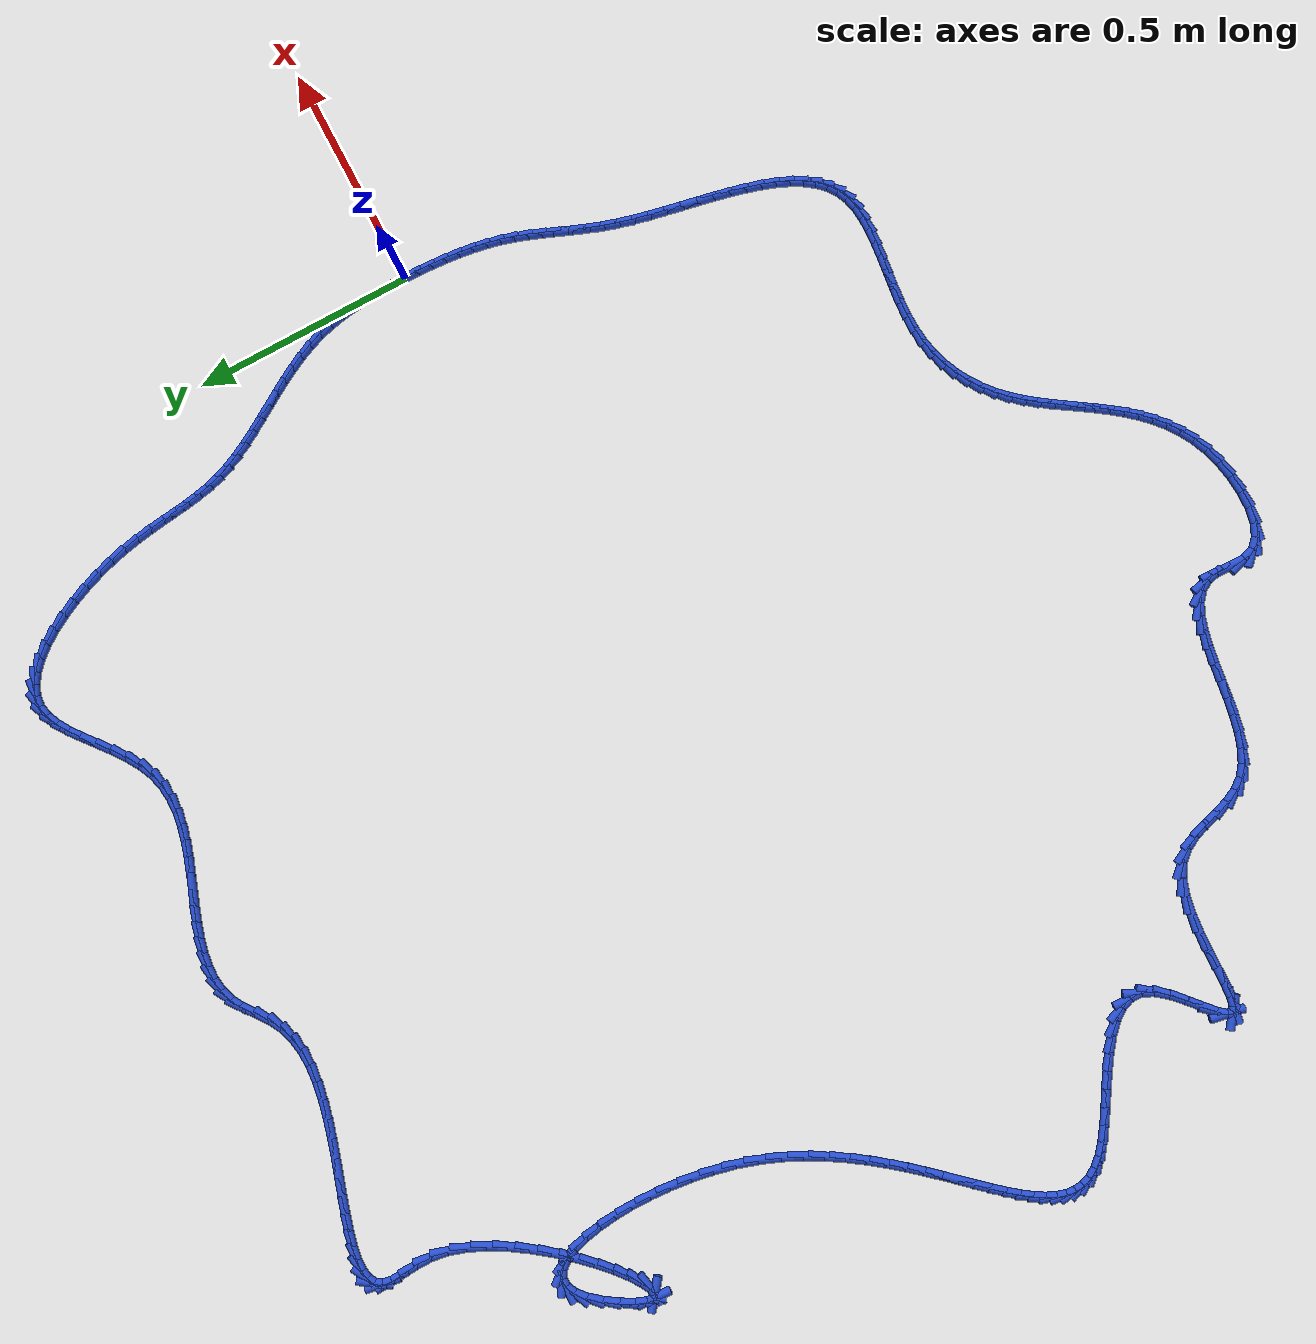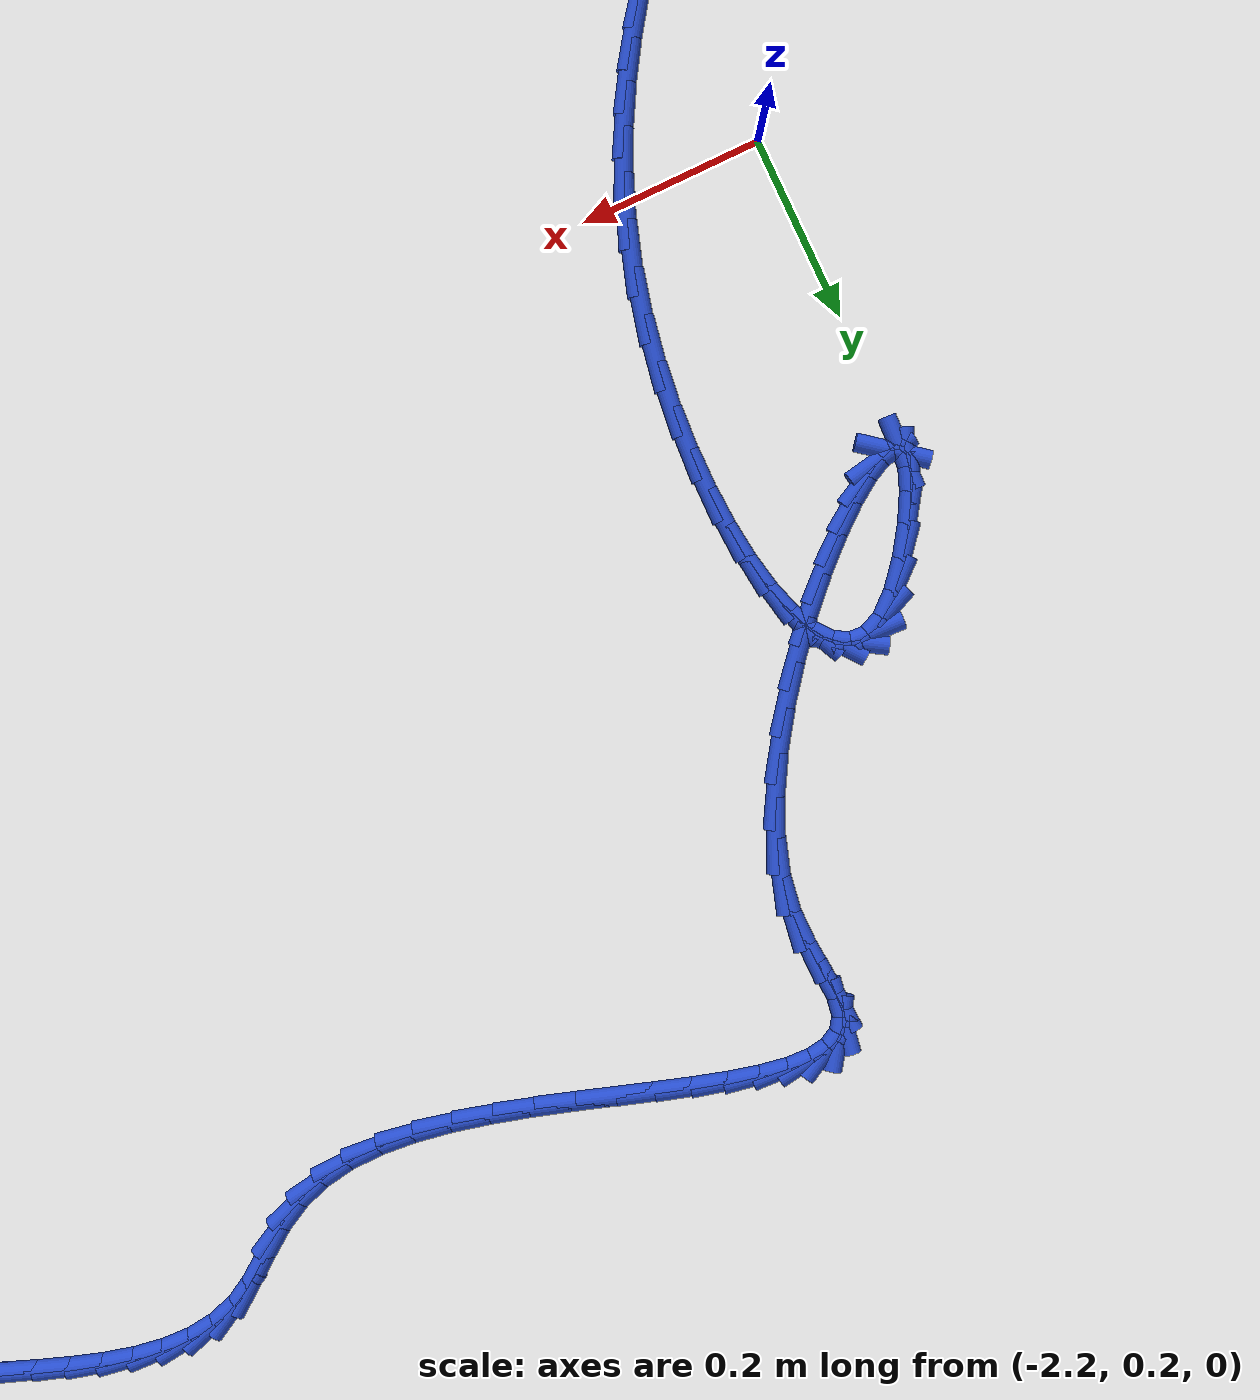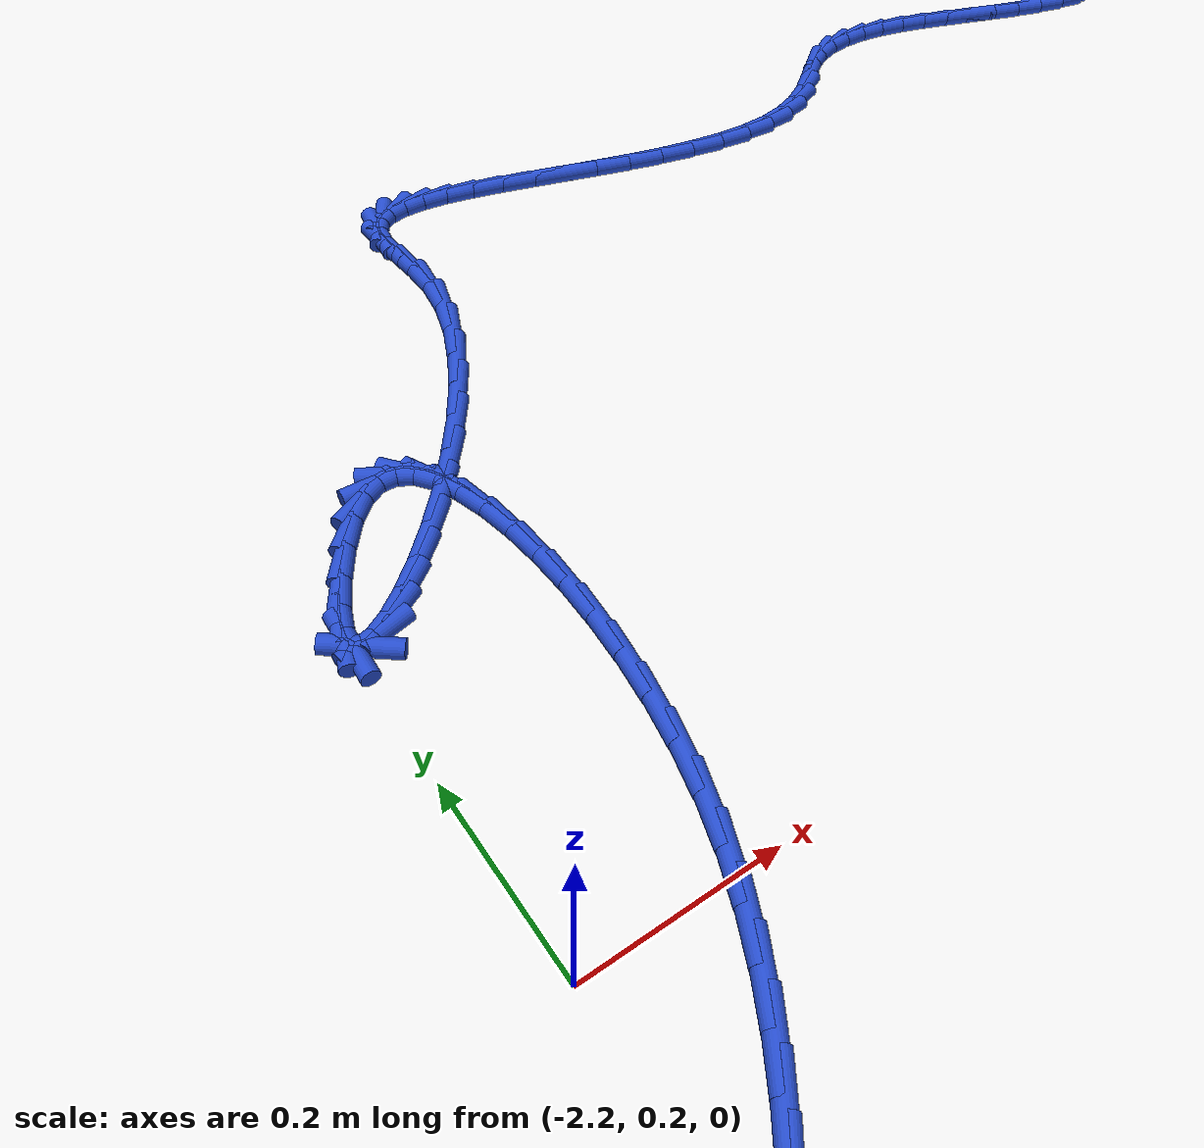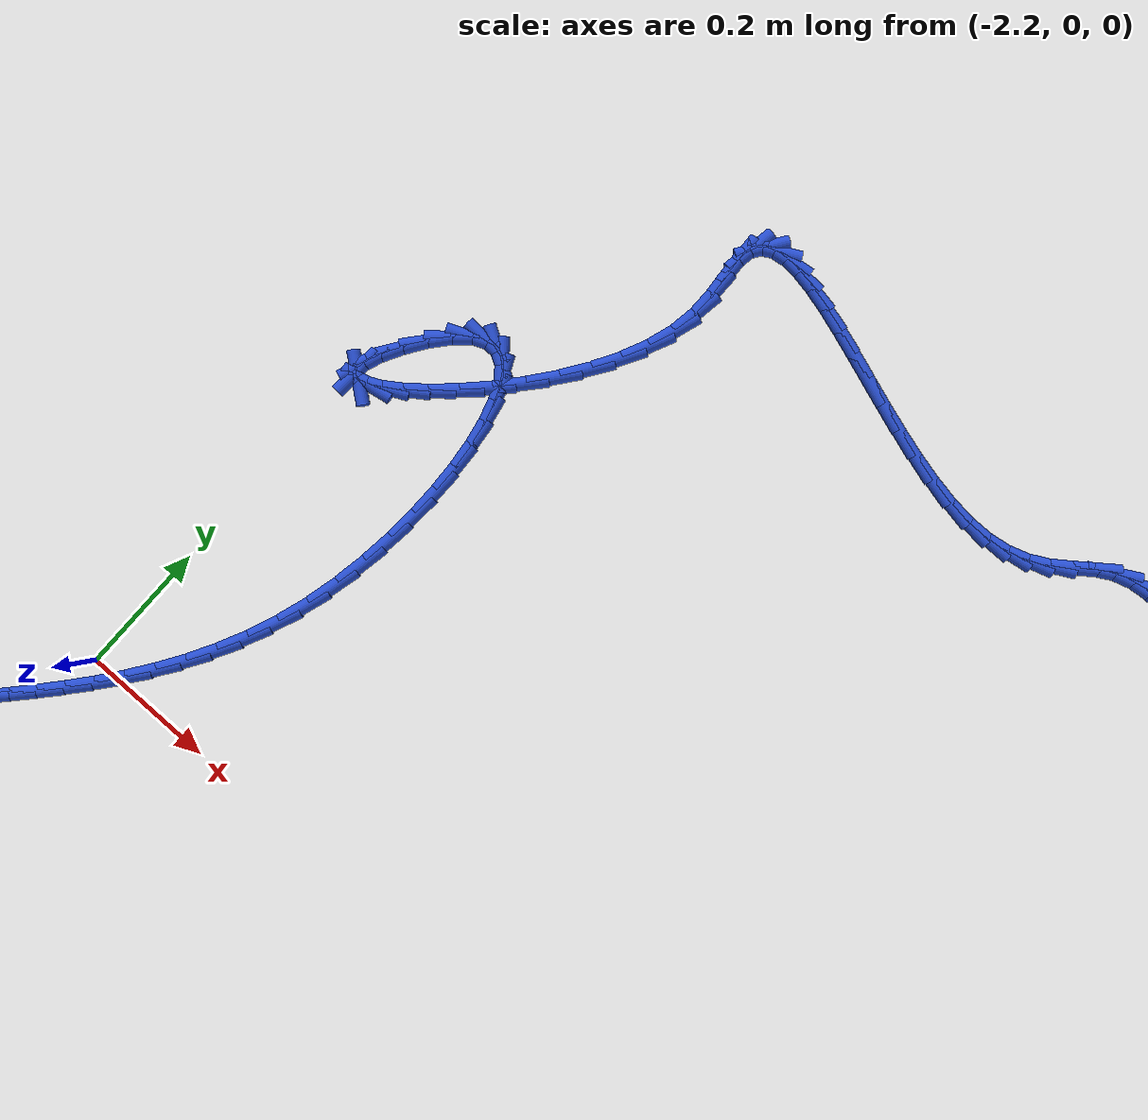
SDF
<sdf version="1.6">
 <world name="default">
  <light name="sun" type="directional">
   <pose>0 0 10 0 -0 0</pose>
   <diffuse>0.8 0.8 0.8 1</diffuse>
   <specular>0.2 0.2 0.2 1</specular>
   <attenuation>
    <range>1000</range>
    <constant>0.9</constant>
    <linear>0.01</linear>
    <quadratic>0.001</quadratic>
   </attenuation>
   <direction>-0.5 0.1 -0.9</direction>
  </light>
  <model name="ground_plane">
   <static>1</static>
   <link name="link">
    <collision name="collision">
     <geometry><plane><normal>0 0 1</normal><size>100 100</size></plane></geometry>
     <surface><friction><ode><mu>100</mu><mu2>50</mu2></ode></friction></surface>
    </collision>
    <visual name="visual">
     <cast_shadows>0</cast_shadows>
     <geometry><plane><normal>0 0 1</normal><size>100 100</size></plane></geometry>
     <material>
      <script><uri>file://media/materials/scripts/gazebo.material</uri><name>Gazebo/WhiteGlow</name></script>
     </material>
    </visual>
   </link>
  </model>
  <gravity>0 0 -9.8</gravity>
  <magnetic_field>6e-06 2.3e-05 -4.2e-05</magnetic_field>
  <atmosphere type="adiabatic"/>
  <physics name="default_physics" default="0" type="ode">
   <max_step_size>0.001</max_step_size>
   <real_time_factor>1</real_time_factor>
   <real_time_update_rate>1000</real_time_update_rate>
  </physics>
  <scene><ambient>0.4 0.4 0.4 1</ambient><background>0.7 0.7 0.7 1</background><shadows>1</shadows></scene>
  <spherical_coordinates>
   <surface_model>EARTH_WGS84</surface_model>
   <latitude_deg>0</latitude_deg>
   <longitude_deg>0</longitude_deg>
   <elevation>0</elevation>
   <heading_deg>0</heading_deg>
  </spherical_coordinates>
  <model name="line">
   <link name="link_0">
    <pose>-1.235990476633475e-17 -4.85722573273506e-17 0.01 0 1.57 1.566100618739235</pose>
    <collision name="collision">
     <geometry><cylinder><radius>0.01</radius><length>0.08</length></cylinder></geometry>
    </collision>
    <visual name="visual">
     <material>
      <script><name>Gazebo/Blue</name><uri>file://media/materials/scripts/gazebo.material</uri></script>
     </material>
     <geometry><cylinder><radius>0.01</radius><length>0.08</length></cylinder></geometry>
    </visual>
   </link>
   <link name="link_1">
    <pose>0.00015219235352785057 0.03241071061593272 0.01 0 1.57 -1.5516855321531333</pose>
    <collision name="collision">
     <geometry><cylinder><radius>0.01</radius><length>0.08</length></cylinder></geometry>
    </collision>
    <visual name="visual">
     <material>
      <script><name>Gazebo/Blue</name><uri>file://media/materials/scripts/gazebo.material</uri></script>
     </material>
     <geometry><cylinder><radius>0.01</radius><length>0.08</length></cylinder></geometry>
    </visual>
   </link>
   <link name="link_2">
    <pose>-0.0004650261547788062 0.06470363078779405 0.01 0 1.57 -1.5196579744192886</pose>
    <collision name="collision">
     <geometry><cylinder><radius>0.01</radius><length>0.08</length></cylinder></geometry>
    </collision>
    <visual name="visual">
     <material>
      <script><name>Gazebo/Blue</name><uri>file://media/materials/scripts/gazebo.material</uri></script>
     </material>
     <geometry><cylinder><radius>0.01</radius><length>0.08</length></cylinder></geometry>
    </visual>
   </link>
   <link name="link_3">
    <pose>-0.002107848509032991 0.09680067660575445 0.01 0 1.57 -1.4791513278105897</pose>
    <collision name="collision">
     <geometry><cylinder><radius>0.01</radius><length>0.08</length></cylinder></geometry>
    </collision>
    <visual name="visual">
     <material>
      <script><name>Gazebo/Blue</name><uri>file://media/materials/scripts/gazebo.material</uri></script>
     </material>
     <geometry><cylinder><radius>0.01</radius><length>0.08</length></cylinder></geometry>
    </visual>
   </link>
   <link name="link_4">
    <pose>-0.005032467693347711 0.1286237641599844 0.01 0 1.57 -1.4299349653032722</pose>
    <collision name="collision">
     <geometry><cylinder><radius>0.01</radius><length>0.08</length></cylinder></geometry>
    </collision>
    <visual name="visual">
     <material>
      <script><name>Gazebo/Blue</name><uri>file://media/materials/scripts/gazebo.material</uri></script>
     </material>
     <geometry><cylinder><radius>0.01</radius><length>0.08</length></cylinder></geometry>
    </visual>
   </link>
   <link name="link_5">
    <pose>-0.009495076691835969 0.16009480954065428 0.01 0 1.57 -1.3718955185037613</pose>
    <collision name="collision">
     <geometry><cylinder><radius>0.01</radius><length>0.08</length></cylinder></geometry>
    </collision>
    <visual name="visual">
     <material>
      <script><name>Gazebo/Blue</name><uri>file://media/materials/scripts/gazebo.material</uri></script>
     </material>
     <geometry><cylinder><radius>0.01</radius><length>0.08</length></cylinder></geometry>
    </visual>
   </link>
   <link name="link_6">
    <pose>-0.015751868488610783 0.1911357288379347 0.01 0 1.57 -1.305152082181441</pose>
    <collision name="collision">
     <geometry><cylinder><radius>0.01</radius><length>0.08</length></cylinder></geometry>
    </collision>
    <visual name="visual">
     <material>
      <script><name>Gazebo/Blue</name><uri>file://media/materials/scripts/gazebo.material</uri></script>
     </material>
     <geometry><cylinder><radius>0.01</radius><length>0.08</length></cylinder></geometry>
    </visual>
   </link>
   <link name="link_7">
    <pose>-0.024059036067785148 0.22166843814199616 0.01 0 1.57 -1.231451777372342</pose>
    <collision name="collision">
     <geometry><cylinder><radius>0.01</radius><length>0.08</length></cylinder></geometry>
    </collision>
    <visual name="visual">
     <material>
      <script><name>Gazebo/Blue</name><uri>file://media/materials/scripts/gazebo.material</uri></script>
     </material>
     <geometry><cylinder><radius>0.01</radius><length>0.08</length></cylinder></geometry>
    </visual>
   </link>
   <link name="link_8">
    <pose>-0.03463335852602965 0.2516240613209322 0.01 0 1.57 -1.1643371102490998</pose>
    <collision name="collision">
     <geometry><cylinder><radius>0.01</radius><length>0.08</length></cylinder></geometry>
    </collision>
    <visual name="visual">
     <material>
      <script><name>Gazebo/Blue</name><uri>file://media/materials/scripts/gazebo.material</uri></script>
     </material>
     <geometry><cylinder><radius>0.01</radius><length>0.08</length></cylinder></geometry>
    </visual>
   </link>
   <link name="link_9">
    <pose>-0.0472894929452368 0.28102766502418547 0.01 0 1.57 -1.1112566570468299</pose>
    <collision name="collision">
     <geometry><cylinder><radius>0.01</radius><length>0.08</length></cylinder></geometry>
    </collision>
    <visual name="visual">
     <material>
      <script><name>Gazebo/Blue</name><uri>file://media/materials/scripts/gazebo.material</uri></script>
     </material>
     <geometry><cylinder><radius>0.01</radius><length>0.08</length></cylinder></geometry>
    </visual>
   </link>
   <link name="link_10">
    <pose>-0.06160701968704749 0.3099592339611886 0.01 0 1.57 -1.071769481423054</pose>
    <collision name="collision">
     <geometry><cylinder><radius>0.01</radius><length>0.08</length></cylinder></geometry>
    </collision>
    <visual name="visual">
     <material>
      <script><name>Gazebo/Blue</name><uri>file://media/materials/scripts/gazebo.material</uri></script>
     </material>
     <geometry><cylinder><radius>0.01</radius><length>0.08</length></cylinder></geometry>
    </visual>
   </link>
   <link name="link_11">
    <pose>-0.07716256321209888 0.33849944339188204 0.01 0 1.57 -1.0452904629396624</pose>
    <collision name="collision">
     <geometry><cylinder><radius>0.01</radius><length>0.08</length></cylinder></geometry>
    </collision>
    <visual name="visual">
     <material>
      <script><name>Gazebo/Blue</name><uri>file://media/materials/scripts/gazebo.material</uri></script>
     </material>
     <geometry><cylinder><radius>0.01</radius><length>0.08</length></cylinder></geometry>
    </visual>
   </link>
   <link name="link_12">
    <pose>-0.09353274798102824 0.36672896857620685 0.01 0 1.57 -1.0313821566657377</pose>
    <collision name="collision">
     <geometry><cylinder><radius>0.01</radius><length>0.08</length></cylinder></geometry>
    </collision>
    <visual name="visual">
     <material>
      <script><name>Gazebo/Blue</name><uri>file://media/materials/scripts/gazebo.material</uri></script>
     </material>
     <geometry><cylinder><radius>0.01</radius><length>0.08</length></cylinder></geometry>
    </visual>
   </link>
   <link name="link_13">
    <pose>-0.11029419845447262 0.3947284847741032 0.01 0 1.57 -1.0298692446438105</pose>
    <collision name="collision">
     <geometry><cylinder><radius>0.01</radius><length>0.08</length></cylinder></geometry>
    </collision>
    <visual name="visual">
     <material>
      <script><name>Gazebo/Blue</name><uri>file://media/materials/scripts/gazebo.material</uri></script>
     </material>
     <geometry><cylinder><radius>0.01</radius><length>0.08</length></cylinder></geometry>
    </visual>
   </link>
   <link name="link_14">
    <pose>-0.1270235390930694 0.4225786672455124 0.01 0 1.57 -1.0408984872431144</pose>
    <collision name="collision">
     <geometry><cylinder><radius>0.01</radius><length>0.08</length></cylinder></geometry>
    </collision>
    <visual name="visual">
     <material>
      <script><name>Gazebo/Blue</name><uri>file://media/materials/scripts/gazebo.material</uri></script>
     </material>
     <geometry><cylinder><radius>0.01</radius><length>0.08</length></cylinder></geometry>
    </visual>
   </link>
   <link name="link_15">
    <pose>-0.14329739435745553 0.4503601912503747 0.01 0 1.57 -1.0649596180846552</pose>
    <collision name="collision">
     <geometry><cylinder><radius>0.01</radius><length>0.08</length></cylinder></geometry>
    </collision>
    <visual name="visual">
     <material>
      <script><name>Gazebo/Blue</name><uri>file://media/materials/scripts/gazebo.material</uri></script>
     </material>
     <geometry><cylinder><radius>0.01</radius><length>0.08</length></cylinder></geometry>
    </visual>
   </link>
   <link name="link_16">
    <pose>-0.15869238870826835 0.478153732048631 0.01 0 1.57 -1.1028650255918955</pose>
    <collision name="collision">
     <geometry><cylinder><radius>0.01</radius><length>0.08</length></cylinder></geometry>
    </collision>
    <visual name="visual">
     <material>
      <script><name>Gazebo/Blue</name><uri>file://media/materials/scripts/gazebo.material</uri></script>
     </material>
     <geometry><cylinder><radius>0.01</radius><length>0.08</length></cylinder></geometry>
    </visual>
   </link>
   <link name="link_17">
    <pose>-0.17278514660614508 0.5060399649002219 0.01 0 1.57 -1.1556649412952094</pose>
    <collision name="collision">
     <geometry><cylinder><radius>0.01</radius><length>0.08</length></cylinder></geometry>
    </collision>
    <visual name="visual">
     <material>
      <script><name>Gazebo/Blue</name><uri>file://media/materials/scripts/gazebo.material</uri></script>
     </material>
     <geometry><cylinder><radius>0.01</radius><length>0.08</length></cylinder></geometry>
    </visual>
   </link>
   <link name="link_18">
    <pose>-0.18515229251172272 0.534099565065088 0.01 0 1.57 -1.2244380104600048</pose>
    <collision name="collision">
     <geometry><cylinder><radius>0.01</radius><length>0.08</length></cylinder></geometry>
    </collision>
    <visual name="visual">
     <material>
      <script><name>Gazebo/Blue</name><uri>file://media/materials/scripts/gazebo.material</uri></script>
     </material>
     <geometry><cylinder><radius>0.01</radius><length>0.08</length></cylinder></geometry>
    </visual>
   </link>
   <link name="link_19">
    <pose>-0.19537089247910183 0.5624132277088669 0.01 0 1.57 -1.3021854720569428</pose>
    <collision name="collision">
     <geometry><cylinder><radius>0.01</radius><length>0.08</length></cylinder></geometry>
    </collision>
    <visual name="visual">
     <material>
      <script><name>Gazebo/Blue</name><uri>file://media/materials/scripts/gazebo.material</uri></script>
     </material>
     <geometry><cylinder><radius>0.01</radius><length>0.08</length></cylinder></geometry>
    </visual>
   </link>
   <link name="link_20">
    <pose>-0.20325974669941613 0.5910725446404158 0.01 0 1.57 -1.3669906924949295</pose>
    <collision name="collision">
     <geometry><cylinder><radius>0.01</radius><length>0.08</length></cylinder></geometry>
    </collision>
    <visual name="visual">
     <material>
      <script><name>Gazebo/Blue</name><uri>file://media/materials/scripts/gazebo.material</uri></script>
     </material>
     <geometry><cylinder><radius>0.01</radius><length>0.08</length></cylinder></geometry>
    </visual>
   </link>
   <link name="link_21">
    <pose>-0.20927925991647964 0.6201980292598265 0.01 0 1.57 -1.4134167884275526</pose>
    <collision name="collision">
     <geometry><cylinder><radius>0.01</radius><length>0.08</length></cylinder></geometry>
    </collision>
    <visual name="visual">
     <material>
      <script><name>Gazebo/Blue</name><uri>file://media/materials/scripts/gazebo.material</uri></script>
     </material>
     <geometry><cylinder><radius>0.01</radius><length>0.08</length></cylinder></geometry>
    </visual>
   </link>
   <link name="link_22">
    <pose>-0.2139950923983609 0.6499149395676381 0.01 0 1.57 -1.4408284535988678</pose>
    <collision name="collision">
     <geometry><cylinder><radius>0.01</radius><length>0.08</length></cylinder></geometry>
    </collision>
    <visual name="visual">
     <material>
      <script><name>Gazebo/Blue</name><uri>file://media/materials/scripts/gazebo.material</uri></script>
     </material>
     <geometry><cylinder><radius>0.01</radius><length>0.08</length></cylinder></geometry>
    </visual>
   </link>
   <link name="link_23">
    <pose>-0.21797290441312867 0.68034853356439 0.01 0 1.57 -1.4497164751411604</pose>
    <collision name="collision">
     <geometry><cylinder><radius>0.01</radius><length>0.08</length></cylinder></geometry>
    </collision>
    <visual name="visual">
     <material>
      <script><name>Gazebo/Blue</name><uri>file://media/materials/scripts/gazebo.material</uri></script>
     </material>
     <geometry><cylinder><radius>0.01</radius><length>0.08</length></cylinder></geometry>
    </visual>
   </link>
   <link name="link_24">
    <pose>-0.22177835622885148 0.7116240692506212 0.01 0 1.57 -1.441301847330977</pose>
    <collision name="collision">
     <geometry><cylinder><radius>0.01</radius><length>0.08</length></cylinder></geometry>
    </collision>
    <visual name="visual">
     <material>
      <script><name>Gazebo/Blue</name><uri>file://media/materials/scripts/gazebo.material</uri></script>
     </material>
     <geometry><cylinder><radius>0.01</radius><length>0.08</length></cylinder></geometry>
    </visual>
   </link>
   <link name="link_25">
    <pose>-0.225977108113598 0.7438668046268709 0.01 0 1.57 -1.4172907986450674</pose>
    <collision name="collision">
     <geometry><cylinder><radius>0.01</radius><length>0.08</length></cylinder></geometry>
    </collision>
    <visual name="visual">
     <material>
      <script><name>Gazebo/Blue</name><uri>file://media/materials/scripts/gazebo.material</uri></script>
     </material>
     <geometry><cylinder><radius>0.01</radius><length>0.08</length></cylinder></geometry>
    </visual>
   </link>
   <link name="link_26">
    <pose>-0.2311348203354369 0.7772019976936786 0.01 0 1.57 -1.379760472157938</pose>
    <collision name="collision">
     <geometry><cylinder><radius>0.01</radius><length>0.08</length></cylinder></geometry>
    </collision>
    <visual name="visual">
     <material>
      <script><name>Gazebo/Blue</name><uri>file://media/materials/scripts/gazebo.material</uri></script>
     </material>
     <geometry><cylinder><radius>0.01</radius><length>0.08</length></cylinder></geometry>
    </visual>
   </link>
   <link name="link_27">
    <pose>-0.23781715316243676 0.8117549064515832 0.01 0 1.57 -1.3315169358083603</pose>
    <collision name="collision">
     <geometry><cylinder><radius>0.01</radius><length>0.08</length></cylinder></geometry>
    </collision>
    <visual name="visual">
     <material>
      <script><name>Gazebo/Blue</name><uri>file://media/materials/scripts/gazebo.material</uri></script>
     </material>
     <geometry><cylinder><radius>0.01</radius><length>0.08</length></cylinder></geometry>
    </visual>
   </link>
   <link name="link_28">
    <pose>-0.24656716783948168 0.8476225204404715 0.01 0 1.57 -1.2808650004285862</pose>
    <collision name="collision">
     <geometry><cylinder><radius>0.01</radius><length>0.08</length></cylinder></geometry>
    </collision>
    <visual name="visual">
     <material>
      <script><name>Gazebo/Blue</name><uri>file://media/materials/scripts/gazebo.material</uri></script>
     </material>
     <geometry><cylinder><radius>0.01</radius><length>0.08</length></cylinder></geometry>
    </visual>
   </link>
   <link name="link_29">
    <pose>-0.2575467567340899 0.8844250361404715 0.01 0 1.57 -1.231289530642241</pose>
    <collision name="collision">
     <geometry><cylinder><radius>0.01</radius><length>0.08</length></cylinder></geometry>
    </collision>
    <visual name="visual">
     <material>
      <script><name>Gazebo/Blue</name><uri>file://media/materials/scripts/gazebo.material</uri></script>
     </material>
     <geometry><cylinder><radius>0.01</radius><length>0.08</length></cylinder></geometry>
    </visual>
   </link>
   <link name="link_30">
    <pose>-0.2706007002910211 0.9213859839529296 0.01 0 1.57 -1.1801029023143292</pose>
    <collision name="collision">
     <geometry><cylinder><radius>0.01</radius><length>0.08</length></cylinder></geometry>
    </collision>
    <visual name="visual">
     <material>
      <script><name>Gazebo/Blue</name><uri>file://media/materials/scripts/gazebo.material</uri></script>
     </material>
     <geometry><cylinder><radius>0.01</radius><length>0.08</length></cylinder></geometry>
    </visual>
   </link>
   <link name="link_31">
    <pose>-0.28556412742650505 0.9577168214629356 0.01 0 1.57 -1.1244365351144154</pose>
    <collision name="collision">
     <geometry><cylinder><radius>0.01</radius><length>0.08</length></cylinder></geometry>
    </collision>
    <visual name="visual">
     <material>
      <script><name>Gazebo/Blue</name><uri>file://media/materials/scripts/gazebo.material</uri></script>
     </material>
     <geometry><cylinder><radius>0.01</radius><length>0.08</length></cylinder></geometry>
    </visual>
   </link>
   <link name="link_32">
    <pose>-0.3022721670567716 0.9926290062555804 0.01 0 1.57 -1.0609370057740528</pose>
    <collision name="collision">
     <geometry><cylinder><radius>0.01</radius><length>0.08</length></cylinder></geometry>
    </collision>
    <visual name="visual">
     <material>
      <script><name>Gazebo/Blue</name><uri>file://media/materials/scripts/gazebo.material</uri></script>
     </material>
     <geometry><cylinder><radius>0.01</radius><length>0.08</length></cylinder></geometry>
    </visual>
   </link>
   <link name="link_33">
    <pose>-0.3205599480980508 1.0253339959159533 0.01 0 1.57 -0.9852098294130419</pose>
    <collision name="collision">
     <geometry><cylinder><radius>0.01</radius><length>0.08</length></cylinder></geometry>
    </collision>
    <visual name="visual">
     <material>
      <script><name>Gazebo/Blue</name><uri>file://media/materials/scripts/gazebo.material</uri></script>
     </material>
     <geometry><cylinder><radius>0.01</radius><length>0.08</length></cylinder></geometry>
    </visual>
   </link>
   <link name="link_34">
    <pose>-0.34026259946657217 1.055043248029145 0.01 0 1.57 -0.8910732900235412</pose>
    <collision name="collision">
     <geometry><cylinder><radius>0.01</radius><length>0.08</length></cylinder></geometry>
    </collision>
    <visual name="visual">
     <material>
      <script><name>Gazebo/Blue</name><uri>file://media/materials/scripts/gazebo.material</uri></script>
     </material>
     <geometry><cylinder><radius>0.01</radius><length>0.08</length></cylinder></geometry>
    </visual>
   </link>
   <link name="link_35">
    <pose>-0.3612152500785656 1.0809682201802453 0.01 0 1.57 -0.769597908262072</pose>
    <collision name="collision">
     <geometry><cylinder><radius>0.01</radius><length>0.08</length></cylinder></geometry>
    </collision>
    <visual name="visual">
     <material>
      <script><name>Gazebo/Blue</name><uri>file://media/materials/scripts/gazebo.material</uri></script>
     </material>
     <geometry><cylinder><radius>0.01</radius><length>0.08</length></cylinder></geometry>
    </visual>
   </link>
   <link name="link_36">
    <pose>-0.38325302885026125 1.1023203699543451 0.01 0 1.57 -0.6083881529841033</pose>
    <collision name="collision">
     <geometry><cylinder><radius>0.01</radius><length>0.08</length></cylinder></geometry>
    </collision>
    <visual name="visual">
     <material>
      <script><name>Gazebo/Blue</name><uri>file://media/materials/scripts/gazebo.material</uri></script>
     </material>
     <geometry><cylinder><radius>0.01</radius><length>0.08</length></cylinder></geometry>
    </visual>
   </link>
   <link name="link_37">
    <pose>-0.40621106469788876 1.1183111549365337 0.01 0 1.57 -0.3933632440185412</pose>
    <collision name="collision">
     <geometry><cylinder><radius>0.01</radius><length>0.08</length></cylinder></geometry>
    </collision>
    <visual name="visual">
     <material>
      <script><name>Gazebo/Blue</name><uri>file://media/materials/scripts/gazebo.material</uri></script>
     </material>
     <geometry><cylinder><radius>0.01</radius><length>0.08</length></cylinder></geometry>
    </visual>
   </link>
   <link name="link_38">
    <pose>-0.4299244865376779 1.1281520327119012 0.01 0 1.57 -0.1188592308754398</pose>
    <collision name="collision">
     <geometry><cylinder><radius>0.01</radius><length>0.08</length></cylinder></geometry>
    </collision>
    <visual name="visual">
     <material>
      <script><name>Gazebo/Blue</name><uri>file://media/materials/scripts/gazebo.material</uri></script>
     </material>
     <geometry><cylinder><radius>0.01</radius><length>0.08</length></cylinder></geometry>
    </visual>
   </link>
   <link name="link_39">
    <pose>-0.45422842328585855 1.1310544608655382 0.01 0 1.57 0.1834991508332692</pose>
    <collision name="collision">
     <geometry><cylinder><radius>0.01</radius><length>0.08</length></cylinder></geometry>
    </collision>
    <visual name="visual">
     <material>
      <script><name>Gazebo/Blue</name><uri>file://media/materials/scripts/gazebo.material</uri></script>
     </material>
     <geometry><cylinder><radius>0.01</radius><length>0.08</length></cylinder></geometry>
    </visual>
   </link>
   <link name="link_40">
    <pose>-0.4789802070878139 1.1264608549065698 0.01 0 1.57 0.41629968458068795</pose>
    <collision name="collision">
     <geometry><cylinder><radius>0.01</radius><length>0.08</length></cylinder></geometry>
    </collision>
    <visual name="visual">
     <material>
      <script><name>Gazebo/Blue</name><uri>file://media/materials/scripts/gazebo.material</uri></script>
     </material>
     <geometry><cylinder><radius>0.01</radius><length>0.08</length></cylinder></geometry>
    </visual>
   </link>
   <link name="link_41">
    <pose>-0.5041818103560564 1.1153181779753298 0.01 0 1.57 0.5606284082201763</pose>
    <collision name="collision">
     <geometry><cylinder><radius>0.01</radius><length>0.08</length></cylinder></geometry>
    </collision>
    <visual name="visual">
     <material>
      <script><name>Gazebo/Blue</name><uri>file://media/materials/scripts/gazebo.material</uri></script>
     </material>
     <geometry><cylinder><radius>0.01</radius><length>0.08</length></cylinder></geometry>
    </visual>
   </link>
   <link name="link_42">
    <pose>-0.5298931333997976 1.0991759590224295 0.01 0 1.57 0.6405676982673846</pose>
    <collision name="collision">
     <geometry><cylinder><radius>0.01</radius><length>0.08</length></cylinder></geometry>
    </collision>
    <visual name="visual">
     <material>
      <script><name>Gazebo/Blue</name><uri>file://media/materials/scripts/gazebo.material</uri></script>
     </material>
     <geometry><cylinder><radius>0.01</radius><length>0.08</length></cylinder></geometry>
    </visual>
   </link>
   <link name="link_43">
    <pose>-0.5561742306519719 1.0795853301929763 0.01 0 1.57 0.6738150242233553</pose>
    <collision name="collision">
     <geometry><cylinder><radius>0.01</radius><length>0.08</length></cylinder></geometry>
    </collision>
    <visual name="visual">
     <material>
      <script><name>Gazebo/Blue</name><uri>file://media/materials/scripts/gazebo.material</uri></script>
     </material>
     <geometry><cylinder><radius>0.01</radius><length>0.08</length></cylinder></geometry>
    </visual>
   </link>
   <link name="link_44">
    <pose>-0.5830851565455125 1.058097423632077 0.01 0 1.57 0.6692693817183377</pose>
    <collision name="collision">
     <geometry><cylinder><radius>0.01</radius><length>0.08</length></cylinder></geometry>
    </collision>
    <visual name="visual">
     <material>
      <script><name>Gazebo/Blue</name><uri>file://media/materials/scripts/gazebo.material</uri></script>
     </material>
     <geometry><cylinder><radius>0.01</radius><length>0.08</length></cylinder></geometry>
    </visual>
   </link>
   <link name="link_45">
    <pose>-0.6106859655133539 1.0362633714848393 0.01 0 1.57 0.6290348099635539</pose>
    <collision name="collision">
     <geometry><cylinder><radius>0.01</radius><length>0.08</length></cylinder></geometry>
    </collision>
    <visual name="visual">
     <material>
      <script><name>Gazebo/Blue</name><uri>file://media/materials/scripts/gazebo.material</uri></script>
     </material>
     <geometry><cylinder><radius>0.01</radius><length>0.08</length></cylinder></geometry>
    </visual>
   </link>
   <link name="link_46">
    <pose>-0.6390367119884288 1.0156343058963704 0.01 0 1.57 0.5498590718017157</pose>
    <collision name="collision">
     <geometry><cylinder><radius>0.01</radius><length>0.08</length></cylinder></geometry>
    </collision>
    <visual name="visual">
     <material>
      <script><name>Gazebo/Blue</name><uri>file://media/materials/scripts/gazebo.material</uri></script>
     </material>
     <geometry><cylinder><radius>0.01</radius><length>0.08</length></cylinder></geometry>
    </visual>
   </link>
   <link name="link_47">
    <pose>-0.6681974504036721 0.9977613590117776 0.01 0 1.57 0.42428861123072037</pose>
    <collision name="collision">
     <geometry><cylinder><radius>0.01</radius><length>0.08</length></cylinder></geometry>
    </collision>
    <visual name="visual">
     <material>
      <script><name>Gazebo/Blue</name><uri>file://media/materials/scripts/gazebo.material</uri></script>
     </material>
     <geometry><cylinder><radius>0.01</radius><length>0.08</length></cylinder></geometry>
    </visual>
   </link>
   <link name="link_48">
    <pose>-0.6982282351920168 0.9841956629761678 0.01 0 1.57 0.25434261055261337</pose>
    <collision name="collision">
     <geometry><cylinder><radius>0.01</radius><length>0.08</length></cylinder></geometry>
    </collision>
    <visual name="visual">
     <material>
      <script><name>Gazebo/Blue</name><uri>file://media/materials/scripts/gazebo.material</uri></script>
     </material>
     <geometry><cylinder><radius>0.01</radius><length>0.08</length></cylinder></geometry>
    </visual>
   </link>
   <link name="link_49">
    <pose>-0.7291592669462265 0.9761544350576148 0.01 0 1.57 0.08898181710906362</pose>
    <collision name="collision">
     <geometry><cylinder><radius>0.01</radius><length>0.08</length></cylinder></geometry>
    </collision>
    <visual name="visual">
     <material>
      <script><name>Gazebo/Blue</name><uri>file://media/materials/scripts/gazebo.material</uri></script>
     </material>
     <geometry><cylinder><radius>0.01</radius><length>0.08</length></cylinder></geometry>
    </visual>
   </link>
   <link name="link_50">
    <pose>-0.760883880210497 0.9733240472622092 0.01 0 1.57 -0.05025954373850041</pose>
    <collision name="collision">
     <geometry><cylinder><radius>0.01</radius><length>0.08</length></cylinder></geometry>
    </collision>
    <visual name="visual">
     <material>
      <script><name>Gazebo/Blue</name><uri>file://media/materials/scripts/gazebo.material</uri></script>
     </material>
     <geometry><cylinder><radius>0.01</radius><length>0.08</length></cylinder></geometry>
    </visual>
   </link>
   <link name="link_51">
    <pose>-0.7932562110636312 0.974952437187709 0.01 0 1.57 -0.1608848822753462</pose>
    <collision name="collision">
     <geometry><cylinder><radius>0.01</radius><length>0.08</length></cylinder></geometry>
    </collision>
    <visual name="visual">
     <material>
      <script><name>Gazebo/Blue</name><uri>file://media/materials/scripts/gazebo.material</uri></script>
     </material>
     <geometry><cylinder><radius>0.01</radius><length>0.08</length></cylinder></geometry>
    </visual>
   </link>
   <link name="link_52">
    <pose>-0.8261303923705751 0.9802875064849106 0.01 0 1.57 -0.24447187759985048</pose>
    <collision name="collision">
     <geometry><cylinder><radius>0.01</radius><length>0.08</length></cylinder></geometry>
    </collision>
    <visual name="visual">
     <material>
      <script><name>Gazebo/Blue</name><uri>file://media/materials/scripts/gazebo.material</uri></script>
     </material>
     <geometry><cylinder><radius>0.01</radius><length>0.08</length></cylinder></geometry>
    </visual>
   </link>
   <link name="link_53">
    <pose>-0.8593605569962735 0.9885771568046094 0.01 0 1.57 -0.30402991967846493</pose>
    <collision name="collision">
     <geometry><cylinder><radius>0.01</radius><length>0.08</length></cylinder></geometry>
    </collision>
    <visual name="visual">
     <material>
      <script><name>Gazebo/Blue</name><uri>file://media/materials/scripts/gazebo.material</uri></script>
     </material>
     <geometry><cylinder><radius>0.01</radius><length>0.08</length></cylinder></geometry>
    </visual>
   </link>
   <link name="link_54">
    <pose>-0.8928008378056719 0.9990692897976022 0.01 0 1.57 -0.3424047617772439</pose>
    <collision name="collision">
     <geometry><cylinder><radius>0.01</radius><length>0.08</length></cylinder></geometry>
    </collision>
    <visual name="visual">
     <material>
      <script><name>Gazebo/Blue</name><uri>file://media/materials/scripts/gazebo.material</uri></script>
     </material>
     <geometry><cylinder><radius>0.01</radius><length>0.08</length></cylinder></geometry>
    </visual>
   </link>
   <link name="link_55">
    <pose>-0.9263053676637159 1.011011807114685 0.01 0 1.57 -0.36157994881714006</pose>
    <collision name="collision">
     <geometry><cylinder><radius>0.01</radius><length>0.08</length></cylinder></geometry>
    </collision>
    <visual name="visual">
     <material>
      <script><name>Gazebo/Blue</name><uri>file://media/materials/scripts/gazebo.material</uri></script>
     </material>
     <geometry><cylinder><radius>0.01</radius><length>0.08</length></cylinder></geometry>
    </visual>
   </link>
   <link name="link_56">
    <pose>-0.9597282794353508 1.0236526104066535 0.01 0 1.57 -0.36242894106869983</pose>
    <collision name="collision">
     <geometry><cylinder><radius>0.01</radius><length>0.08</length></cylinder></geometry>
    </collision>
    <visual name="visual">
     <material>
      <script><name>Gazebo/Blue</name><uri>file://media/materials/scripts/gazebo.material</uri></script>
     </material>
     <geometry><cylinder><radius>0.01</radius><length>0.08</length></cylinder></geometry>
    </visual>
   </link>
   <link name="link_57">
    <pose>-0.9929237059855215 1.036239601324304 0.01 0 1.57 -0.3446148510717042</pose>
    <collision name="collision">
     <geometry><cylinder><radius>0.01</radius><length>0.08</length></cylinder></geometry>
    </collision>
    <visual name="visual">
     <material>
      <script><name>Gazebo/Blue</name><uri>file://media/materials/scripts/gazebo.material</uri></script>
     </material>
     <geometry><cylinder><radius>0.01</radius><length>0.08</length></cylinder></geometry>
    </visual>
   </link>
   <link name="link_58">
    <pose>-1.0257457801791738 1.0480206815184325 0.01 0 1.57 -0.3065028198799078</pose>
    <collision name="collision">
     <geometry><cylinder><radius>0.01</radius><length>0.08</length></cylinder></geometry>
    </collision>
    <visual name="visual">
     <material>
      <script><name>Gazebo/Blue</name><uri>file://media/materials/scripts/gazebo.material</uri></script>
     </material>
     <geometry><cylinder><radius>0.01</radius><length>0.08</length></cylinder></geometry>
    </visual>
   </link>
   <link name="link_59">
    <pose>-1.0580486348812534 1.0582437526398354 0.01 0 1.57 -0.2450834251346604</pose>
    <collision name="collision">
     <geometry><cylinder><radius>0.01</radius><length>0.08</length></cylinder></geometry>
    </collision>
    <visual name="visual">
     <material>
      <script><name>Gazebo/Blue</name><uri>file://media/materials/scripts/gazebo.material</uri></script>
     </material>
     <geometry><cylinder><radius>0.01</radius><length>0.08</length></cylinder></geometry>
    </visual>
   </link>
   <link name="link_60">
    <pose>-1.0896864029567053 1.0661567163393082 0.01 0 1.57 -0.15607536954439294</pose>
    <collision name="collision">
     <geometry><cylinder><radius>0.01</radius><length>0.08</length></cylinder></geometry>
    </collision>
    <visual name="visual">
     <material>
      <script><name>Gazebo/Blue</name><uri>file://media/materials/scripts/gazebo.material</uri></script>
     </material>
     <geometry><cylinder><radius>0.01</radius><length>0.08</length></cylinder></geometry>
    </visual>
   </link>
   <link name="link_61">
    <pose>-1.1205132172704748 1.0710074742676476 0.01 0 1.57 -0.03468491362838</pose>
    <collision name="collision">
     <geometry><cylinder><radius>0.01</radius><length>0.08</length></cylinder></geometry>
    </collision>
    <visual name="visual">
     <material>
      <script><name>Gazebo/Blue</name><uri>file://media/materials/scripts/gazebo.material</uri></script>
     </material>
     <geometry><cylinder><radius>0.01</radius><length>0.08</length></cylinder></geometry>
    </visual>
   </link>
   <link name="link_62">
    <pose>-1.1503832106875076 1.07204392807565 0.01 0 1.57 0.12209660096683038</pose>
    <collision name="collision">
     <geometry><cylinder><radius>0.01</radius><length>0.08</length></cylinder></geometry>
    </collision>
    <visual name="visual">
     <material>
      <script><name>Gazebo/Blue</name><uri>file://media/materials/scripts/gazebo.material</uri></script>
     </material>
     <geometry><cylinder><radius>0.01</radius><length>0.08</length></cylinder></geometry>
    </visual>
   </link>
   <link name="link_63">
    <pose>-1.179150516072749 1.0685139794141103 0.01 0 1.57 0.31110159453877956</pose>
    <collision name="collision">
     <geometry><cylinder><radius>0.01</radius><length>0.08</length></cylinder></geometry>
    </collision>
    <visual name="visual">
     <material>
      <script><name>Gazebo/Blue</name><uri>file://media/materials/scripts/gazebo.material</uri></script>
     </material>
     <geometry><cylinder><radius>0.01</radius><length>0.08</length></cylinder></geometry>
    </visual>
   </link>
   <link name="link_64">
    <pose>-1.206669266291144 1.0596655299338253 0.01 0 1.57 0.5175995134805523</pose>
    <collision name="collision">
     <geometry><cylinder><radius>0.01</radius><length>0.08</length></cylinder></geometry>
    </collision>
    <visual name="visual">
     <material>
      <script><name>Gazebo/Blue</name><uri>file://media/materials/scripts/gazebo.material</uri></script>
     </material>
     <geometry><cylinder><radius>0.01</radius><length>0.08</length></cylinder></geometry>
    </visual>
   </link>
   <link name="link_65">
    <pose>-1.232804659422792 1.044784591988934 0.01 0 1.57 0.6555652553825779</pose>
    <collision name="collision">
     <geometry><cylinder><radius>0.01</radius><length>0.08</length></cylinder></geometry>
    </collision>
    <visual name="visual">
     <material>
      <script><name>Gazebo/Blue</name><uri>file://media/materials/scripts/gazebo.material</uri></script>
     </material>
     <geometry><cylinder><radius>0.01</radius><length>0.08</length></cylinder></geometry>
    </visual>
   </link>
   <link name="link_66">
    <pose>-1.258061829822408 1.0253612400490868 0.01 0 1.57 0.6363050705771549</pose>
    <collision name="collision">
     <geometry><cylinder><radius>0.01</radius><length>0.08</length></cylinder></geometry>
    </collision>
    <visual name="visual">
     <material>
      <script><name>Gazebo/Blue</name><uri>file://media/materials/scripts/gazebo.material</uri></script>
     </material>
     <geometry><cylinder><radius>0.01</radius><length>0.08</length></cylinder></geometry>
    </visual>
   </link>
   <link name="link_67">
    <pose>-1.2839239353646603 1.0062538934817673 0.01 0 1.57 0.49170861377376074</pose>
    <collision name="collision">
     <geometry><cylinder><radius>0.01</radius><length>0.08</length></cylinder></geometry>
    </collision>
    <visual name="visual">
     <material>
      <script><name>Gazebo/Blue</name><uri>file://media/materials/scripts/gazebo.material</uri></script>
     </material>
     <geometry><cylinder><radius>0.01</radius><length>0.08</length></cylinder></geometry>
    </visual>
   </link>
   <link name="link_68">
    <pose>-1.3116494786950115 0.9914045119575835 0.01 0 1.57 0.32426076989597935</pose>
    <collision name="collision">
     <geometry><cylinder><radius>0.01</radius><length>0.08</length></cylinder></geometry>
    </collision>
    <visual name="visual">
     <material>
      <script><name>Gazebo/Blue</name><uri>file://media/materials/scripts/gazebo.material</uri></script>
     </material>
     <geometry><cylinder><radius>0.01</radius><length>0.08</length></cylinder></geometry>
    </visual>
   </link>
   <link name="link_69">
    <pose>-1.3416207906851785 0.9813304106114602 0.01 0 1.57 0.16456609002247868</pose>
    <collision name="collision">
     <geometry><cylinder><radius>0.01</radius><length>0.08</length></cylinder></geometry>
    </collision>
    <visual name="visual">
     <material>
      <script><name>Gazebo/Blue</name><uri>file://media/materials/scripts/gazebo.material</uri></script>
     </material>
     <geometry><cylinder><radius>0.01</radius><length>0.08</length></cylinder></geometry>
    </visual>
   </link>
   <link name="link_70">
    <pose>-1.3740650473435598 0.9759424592775572 0.01 0 1.57 0.023366383114004758</pose>
    <collision name="collision">
     <geometry><cylinder><radius>0.01</radius><length>0.08</length></cylinder></geometry>
    </collision>
    <visual name="visual">
     <material>
      <script><name>Gazebo/Blue</name><uri>file://media/materials/scripts/gazebo.material</uri></script>
     </material>
     <geometry><cylinder><radius>0.01</radius><length>0.08</length></cylinder></geometry>
    </visual>
   </link>
   <link name="link_71">
    <pose>-1.4091711572137604 0.9751220071402835 0.01 0 1.57 -0.08705940791361798</pose>
    <collision name="collision">
     <geometry><cylinder><radius>0.01</radius><length>0.08</length></cylinder></geometry>
    </collision>
    <visual name="visual">
     <material>
      <script><name>Gazebo/Blue</name><uri>file://media/materials/scripts/gazebo.material</uri></script>
     </material>
     <geometry><cylinder><radius>0.01</radius><length>0.08</length></cylinder></geometry>
    </visual>
   </link>
   <link name="link_72">
    <pose>-1.4466668438716304 0.9783946317128341 0.01 0 1.57 -0.16773106625651762</pose>
    <collision name="collision">
     <geometry><cylinder><radius>0.01</radius><length>0.08</length></cylinder></geometry>
    </collision>
    <visual name="visual">
     <material>
      <script><name>Gazebo/Blue</name><uri>file://media/materials/scripts/gazebo.material</uri></script>
     </material>
     <geometry><cylinder><radius>0.01</radius><length>0.08</length></cylinder></geometry>
    </visual>
   </link>
   <link name="link_73">
    <pose>-1.4859743520786806 0.9850502551512327 0.01 0 1.57 -0.22609242675220548</pose>
    <collision name="collision">
     <geometry><cylinder><radius>0.01</radius><length>0.08</length></cylinder></geometry>
    </collision>
    <visual name="visual">
     <material>
      <script><name>Gazebo/Blue</name><uri>file://media/materials/scripts/gazebo.material</uri></script>
     </material>
     <geometry><cylinder><radius>0.01</radius><length>0.08</length></cylinder></geometry>
    </visual>
   </link>
   <link name="link_74">
    <pose>-1.5265104663654756 0.9943745874284855 0.01 0 1.57 -0.2673237663432125</pose>
    <collision name="collision">
     <geometry><cylinder><radius>0.01</radius><length>0.08</length></cylinder></geometry>
    </collision>
    <visual name="visual">
     <material>
      <script><name>Gazebo/Blue</name><uri>file://media/materials/scripts/gazebo.material</uri></script>
     </material>
     <geometry><cylinder><radius>0.01</radius><length>0.08</length></cylinder></geometry>
    </visual>
   </link>
   <link name="link_75">
    <pose>-1.56769197126258 1.0056533385175987 0.01 0 1.57 -0.29469629398357206</pose>
    <collision name="collision">
     <geometry><cylinder><radius>0.01</radius><length>0.08</length></cylinder></geometry>
    </collision>
    <visual name="visual">
     <material>
      <script><name>Gazebo/Blue</name><uri>file://media/materials/scripts/gazebo.material</uri></script>
     </material>
     <geometry><cylinder><radius>0.01</radius><length>0.08</length></cylinder></geometry>
    </visual>
   </link>
   <link name="link_76">
    <pose>-1.6089356513005593 1.0181722183915798 0.01 0 1.57 -0.3100030523345195</pose>
    <collision name="collision">
     <geometry><cylinder><radius>0.01</radius><length>0.08</length></cylinder></geometry>
    </collision>
    <visual name="visual">
     <material>
      <script><name>Gazebo/Blue</name><uri>file://media/materials/scripts/gazebo.material</uri></script>
     </material>
     <geometry><cylinder><radius>0.01</radius><length>0.08</length></cylinder></geometry>
    </visual>
   </link>
   <link name="link_77">
    <pose>-1.6496582910099777 1.0312169370234345 0.01 0 1.57 -0.31378192407972205</pose>
    <collision name="collision">
     <geometry><cylinder><radius>0.01</radius><length>0.08</length></cylinder></geometry>
    </collision>
    <visual name="visual">
     <material>
      <script><name>Gazebo/Blue</name><uri>file://media/materials/scripts/gazebo.material</uri></script>
     </material>
     <geometry><cylinder><radius>0.01</radius><length>0.08</length></cylinder></geometry>
    </visual>
   </link>
   <link name="link_78">
    <pose>-1.6892766749214 1.0440732043861694 0.01 0 1.57 -0.3052876605009464</pose>
    <collision name="collision">
     <geometry><cylinder><radius>0.01</radius><length>0.08</length></cylinder></geometry>
    </collision>
    <visual name="visual">
     <material>
      <script><name>Gazebo/Blue</name><uri>file://media/materials/scripts/gazebo.material</uri></script>
     </material>
     <geometry><cylinder><radius>0.01</radius><length>0.08</length></cylinder></geometry>
    </visual>
   </link>
   <link name="link_79">
    <pose>-1.727207587565391 1.0560267304527906 0.01 0 1.57 -0.2821288381428502</pose>
    <collision name="collision">
     <geometry><cylinder><radius>0.01</radius><length>0.08</length></cylinder></geometry>
    </collision>
    <visual name="visual">
     <material>
      <script><name>Gazebo/Blue</name><uri>file://media/materials/scripts/gazebo.material</uri></script>
     </material>
     <geometry><cylinder><radius>0.01</radius><length>0.08</length></cylinder></geometry>
    </visual>
   </link>
   <link name="link_80">
    <pose>-1.762867813472515 1.0663632251963053 0.01 0 1.57 -0.23933606349010128</pose>
    <collision name="collision">
     <geometry><cylinder><radius>0.01</radius><length>0.08</length></cylinder></geometry>
    </collision>
    <visual name="visual">
     <material>
      <script><name>Gazebo/Blue</name><uri>file://media/materials/scripts/gazebo.material</uri></script>
     </material>
     <geometry><cylinder><radius>0.01</radius><length>0.08</length></cylinder></geometry>
    </visual>
   </link>
   <link name="link_81">
    <pose>-1.7956741371733385 1.0743683985897199 0.01 0 1.57 -0.1672911689909195</pose>
    <collision name="collision">
     <geometry><cylinder><radius>0.01</radius><length>0.08</length></cylinder></geometry>
    </collision>
    <visual name="visual">
     <material>
      <script><name>Gazebo/Blue</name><uri>file://media/materials/scripts/gazebo.material</uri></script>
     </material>
     <geometry><cylinder><radius>0.01</radius><length>0.08</length></cylinder></geometry>
    </visual>
   </link>
   <link name="link_82">
    <pose>-1.8250433431984248 1.0793279606060406 0.01 0 1.57 -0.04729070886477995</pose>
    <collision name="collision">
     <geometry><cylinder><radius>0.01</radius><length>0.08</length></cylinder></geometry>
    </collision>
    <visual name="visual">
     <material>
      <script><name>Gazebo/Blue</name><uri>file://media/materials/scripts/gazebo.material</uri></script>
     </material>
     <geometry><cylinder><radius>0.01</radius><length>0.08</length></cylinder></geometry>
    </visual>
   </link>
   <link name="link_83">
    <pose>-1.8503922160783395 1.0805276212182744 0.01 0 1.57 0.15655264928805063</pose>
    <collision name="collision">
     <geometry><cylinder><radius>0.01</radius><length>0.08</length></cylinder></geometry>
    </collision>
    <visual name="visual">
     <material>
      <script><name>Gazebo/Blue</name><uri>file://media/materials/scripts/gazebo.material</uri></script>
     </material>
     <geometry><cylinder><radius>0.01</radius><length>0.08</length></cylinder></geometry>
    </visual>
   </link>
   <link name="link_84">
    <pose>-1.871137540343647 1.0772530903994273 0.01 0 1.57 0.4981831342453082</pose>
    <collision name="collision">
     <geometry><cylinder><radius>0.01</radius><length>0.08</length></cylinder></geometry>
    </collision>
    <visual name="visual">
     <material>
      <script><name>Gazebo/Blue</name><uri>file://media/materials/scripts/gazebo.material</uri></script>
     </material>
     <geometry><cylinder><radius>0.01</radius><length>0.08</length></cylinder></geometry>
    </visual>
   </link>
   <link name="link_85">
    <pose>-1.8866961005249119 1.0687900781225061 0.01 0 1.57 0.9726755317891169</pose>
    <collision name="collision">
     <geometry><cylinder><radius>0.01</radius><length>0.08</length></cylinder></geometry>
    </collision>
    <visual name="visual">
     <material>
      <script><name>Gazebo/Blue</name><uri>file://media/materials/scripts/gazebo.material</uri></script>
     </material>
     <geometry><cylinder><radius>0.01</radius><length>0.08</length></cylinder></geometry>
    </visual>
   </link>
   <link name="link_86">
    <pose>-1.8964846811526996 1.0544242943605169 0.01 0 1.57 1.4064694968007687</pose>
    <collision name="collision">
     <geometry><cylinder><radius>0.01</radius><length>0.08</length></cylinder></geometry>
    </collision>
    <visual name="visual">
     <material>
      <script><name>Gazebo/Blue</name><uri>file://media/materials/scripts/gazebo.material</uri></script>
     </material>
     <geometry><cylinder><radius>0.01</radius><length>0.08</length></cylinder></geometry>
    </visual>
   </link>
   <link name="link_87">
    <pose>-1.8999609698094233 1.033460330338864 0.01 0 1.57 -1.5132455910562665</pose>
    <collision name="collision">
     <geometry><cylinder><radius>0.01</radius><length>0.08</length></cylinder></geometry>
    </collision>
    <visual name="visual">
     <material>
      <script><name>Gazebo/Blue</name><uri>file://media/materials/scripts/gazebo.material</uri></script>
     </material>
     <geometry><cylinder><radius>0.01</radius><length>0.08</length></cylinder></geometry>
    </visual>
   </link>
   <link name="link_88">
    <pose>-1.8983807500420453 1.006032796125245 0.01 0 1.57 -1.4816029275184341</pose>
    <collision name="collision">
     <geometry><cylinder><radius>0.01</radius><length>0.08</length></cylinder></geometry>
    </collision>
    <visual name="visual">
     <material>
      <script><name>Gazebo/Blue</name><uri>file://media/materials/scripts/gazebo.material</uri></script>
     </material>
     <geometry><cylinder><radius>0.01</radius><length>0.08</length></cylinder></geometry>
    </visual>
   </link>
   <link name="link_89">
    <pose>-1.8954635941579328 0.9734136109938082 0.01 0 1.57 -1.561022737656933</pose>
    <collision name="collision">
     <geometry><cylinder><radius>0.01</radius><length>0.08</length></cylinder></geometry>
    </collision>
    <visual name="visual">
     <material>
      <script><name>Gazebo/Blue</name><uri>file://media/materials/scripts/gazebo.material</uri></script>
     </material>
     <geometry><cylinder><radius>0.01</radius><length>0.08</length></cylinder></geometry>
    </visual>
   </link>
   <link name="link_90">
    <pose>-1.8951072703981815 0.9369569512202924 0.01 0 1.57 1.4214436407326319</pose>
    <collision name="collision">
     <geometry><cylinder><radius>0.01</radius><length>0.08</length></cylinder></geometry>
    </collision>
    <visual name="visual">
     <material>
      <script><name>Gazebo/Blue</name><uri>file://media/materials/scripts/gazebo.material</uri></script>
     </material>
     <geometry><cylinder><radius>0.01</radius><length>0.08</length></cylinder></geometry>
    </visual>
   </link>
   <link name="link_91">
    <pose>-1.900970496354553 0.897991696139016 0.01 0 1.57 1.2628480574588812</pose>
    <collision name="collision">
     <geometry><cylinder><radius>0.01</radius><length>0.08</length></cylinder></geometry>
    </collision>
    <visual name="visual">
     <material>
      <script><name>Gazebo/Blue</name><uri>file://media/materials/scripts/gazebo.material</uri></script>
     </material>
     <geometry><cylinder><radius>0.01</radius><length>0.08</length></cylinder></geometry>
    </visual>
   </link>
   <link name="link_92">
    <pose>-1.913836075319578 0.8575423885942547 0.01 0 1.57 1.1429241148706655</pose>
    <collision name="collision">
     <geometry><cylinder><radius>0.01</radius><length>0.08</length></cylinder></geometry>
    </collision>
    <visual name="visual">
     <material>
      <script><name>Gazebo/Blue</name><uri>file://media/materials/scripts/gazebo.material</uri></script>
     </material>
     <geometry><cylinder><radius>0.01</radius><length>0.08</length></cylinder></geometry>
    </visual>
   </link>
   <link name="link_93">
    <pose>-1.9325842839123513 0.8164322412688995 0.01 0 1.57 1.0502441468076873</pose>
    <collision name="collision">
     <geometry><cylinder><radius>0.01</radius><length>0.08</length></cylinder></geometry>
    </collision>
    <visual name="visual">
     <material>
      <script><name>Gazebo/Blue</name><uri>file://media/materials/scripts/gazebo.material</uri></script>
     </material>
     <geometry><cylinder><radius>0.01</radius><length>0.08</length></cylinder></geometry>
    </visual>
   </link>
   <link name="link_94">
    <pose>-1.9560615052057686 0.7754808801454685 0.01 0 1.57 0.9758295506851785</pose>
    <collision name="collision">
     <geometry><cylinder><radius>0.01</radius><length>0.08</length></cylinder></geometry>
    </collision>
    <visual name="visual">
     <material>
      <script><name>Gazebo/Blue</name><uri>file://media/materials/scripts/gazebo.material</uri></script>
     </material>
     <geometry><cylinder><radius>0.01</radius><length>0.08</length></cylinder></geometry>
    </visual>
   </link>
   <link name="link_95">
    <pose>-1.9831141222727269 0.7355079312064805 0.01 0 1.57 0.9133080258040378</pose>
    <collision name="collision">
     <geometry><cylinder><radius>0.01</radius><length>0.08</length></cylinder></geometry>
    </collision>
    <visual name="visual">
     <material>
      <script><name>Gazebo/Blue</name><uri>file://media/materials/scripts/gazebo.material</uri></script>
     </material>
     <geometry><cylinder><radius>0.01</radius><length>0.08</length></cylinder></geometry>
    </visual>
   </link>
   <link name="link_96">
    <pose>-2.0125885181861225 0.6973330204344542 0.01 0 1.57 0.8578908628230701</pose>
    <collision name="collision">
     <geometry><cylinder><radius>0.01</radius><length>0.08</length></cylinder></geometry>
    </collision>
    <visual name="visual">
     <material>
      <script><name>Gazebo/Blue</name><uri>file://media/materials/scripts/gazebo.material</uri></script>
     </material>
     <geometry><cylinder><radius>0.01</radius><length>0.08</length></cylinder></geometry>
    </visual>
   </link>
   <link name="link_97">
    <pose>-2.0433310760188506 0.6617757738119078 0.01 0 1.57 0.8054480744735907</pose>
    <collision name="collision">
     <geometry><cylinder><radius>0.01</radius><length>0.08</length></cylinder></geometry>
    </collision>
    <visual name="visual">
     <material>
      <script><name>Gazebo/Blue</name><uri>file://media/materials/scripts/gazebo.material</uri></script>
     </material>
     <geometry><cylinder><radius>0.01</radius><length>0.08</length></cylinder></geometry>
    </visual>
   </link>
   <link name="link_98">
    <pose>-2.0741881788438077 0.62965581732136 0.01 0 1.57 0.7515180291842666</pose>
    <collision name="collision">
     <geometry><cylinder><radius>0.01</radius><length>0.08</length></cylinder></geometry>
    </collision>
    <visual name="visual">
     <material>
      <script><name>Gazebo/Blue</name><uri>file://media/materials/scripts/gazebo.material</uri></script>
     </material>
     <geometry><cylinder><radius>0.01</radius><length>0.08</length></cylinder></geometry>
    </visual>
   </link>
   <link name="link_99">
    <pose>-2.10400620973389 0.6017927769453294 0.01 0 1.57 0.6897050750005533</pose>
    <collision name="collision">
     <geometry><cylinder><radius>0.01</radius><length>0.08</length></cylinder></geometry>
    </collision>
    <visual name="visual">
     <material>
      <script><name>Gazebo/Blue</name><uri>file://media/materials/scripts/gazebo.material</uri></script>
     </material>
     <geometry><cylinder><radius>0.01</radius><length>0.08</length></cylinder></geometry>
    </visual>
   </link>
   <link name="link_100">
    <pose>-2.1316315517619926 0.5790062786663344 0.01 0 1.57 0.6078177018483295</pose>
    <collision name="collision">
     <geometry><cylinder><radius>0.01</radius><length>0.08</length></cylinder></geometry>
    </collision>
    <visual name="visual">
     <material>
      <script><name>Gazebo/Blue</name><uri>file://media/materials/scripts/gazebo.material</uri></script>
     </material>
     <geometry><cylinder><radius>0.01</radius><length>0.08</length></cylinder></geometry>
    </visual>
   </link>
   <link name="link_101">
    <pose>-2.155910588001014 0.5621159484668936 0.01 0 1.57 0.4751075353014911</pose>
    <collision name="collision">
     <geometry><cylinder><radius>0.01</radius><length>0.08</length></cylinder></geometry>
    </collision>
    <visual name="visual">
     <material>
      <script><name>Gazebo/Blue</name><uri>file://media/materials/scripts/gazebo.material</uri></script>
     </material>
     <geometry><cylinder><radius>0.01</radius><length>0.08</length></cylinder></geometry>
    </visual>
   </link>
   <link name="link_102">
    <pose>-2.175689701523847 0.5519414123295256 0.01 0 1.57 0.18470302898970317</pose>
    <collision name="collision">
     <geometry><cylinder><radius>0.01</radius><length>0.08</length></cylinder></geometry>
    </collision>
    <visual name="visual">
     <material>
      <script><name>Gazebo/Blue</name><uri>file://media/materials/scripts/gazebo.material</uri></script>
     </material>
     <geometry><cylinder><radius>0.01</radius><length>0.08</length></cylinder></geometry>
    </visual>
   </link>
   <link name="link_103">
    <pose>-2.1898152754033906 0.5493022962367486 0.01 0 1.57 -0.663068607938551</pose>
    <collision name="collision">
     <geometry><cylinder><radius>0.01</radius><length>0.08</length></cylinder></geometry>
    </collision>
    <visual name="visual">
     <material>
      <script><name>Gazebo/Blue</name><uri>file://media/materials/scripts/gazebo.material</uri></script>
     </material>
     <geometry><cylinder><radius>0.01</radius><length>0.08</length></cylinder></geometry>
    </visual>
   </link>
   <link name="link_104">
    <pose>-2.1971336927125398 0.5550182261710815 0.01 0 1.57 1.5276882605667035</pose>
    <collision name="collision">
     <geometry><cylinder><radius>0.01</radius><length>0.08</length></cylinder></geometry>
    </collision>
    <visual name="visual">
     <material>
      <script><name>Gazebo/Blue</name><uri>file://media/materials/scripts/gazebo.material</uri></script>
     </material>
     <geometry><cylinder><radius>0.01</radius><length>0.08</length></cylinder></geometry>
    </visual>
   </link>
   <link name="link_105">
    <pose>-2.1964913934520647 0.5699087421375357 0.01 0 1.57 1.2068091852266547</pose>
    <collision name="collision">
     <geometry><cylinder><radius>0.01</radius><length>0.08</length></cylinder></geometry>
    </collision>
    <visual name="visual">
     <material>
      <script><name>Gazebo/Blue</name><uri>file://media/materials/scripts/gazebo.material</uri></script>
     </material>
     <geometry><cylinder><radius>0.01</radius><length>0.08</length></cylinder></geometry>
    </visual>
   </link>
   <link name="link_106">
    <pose>-2.187385911107536 0.5938100452249053 0.01 0 1.57 1.076481109464602</pose>
    <collision name="collision">
     <geometry><cylinder><radius>0.01</radius><length>0.08</length></cylinder></geometry>
    </collision>
    <visual name="visual">
     <material>
      <script><name>Gazebo/Blue</name><uri>file://media/materials/scripts/gazebo.material</uri></script>
     </material>
     <geometry><cylinder><radius>0.01</radius><length>0.08</length></cylinder></geometry>
    </visual>
   </link>
   <link name="link_107">
    <pose>-2.171581186140828 0.6231354084297489 0.01 0 1.57 0.983516081887218</pose>
    <collision name="collision">
     <geometry><cylinder><radius>0.01</radius><length>0.08</length></cylinder></geometry>
    </collision>
    <visual name="visual">
     <material>
      <script><name>Gazebo/Blue</name><uri>file://media/materials/scripts/gazebo.material</uri></script>
     </material>
     <geometry><cylinder><radius>0.01</radius><length>0.08</length></cylinder></geometry>
    </visual>
   </link>
   <link name="link_108">
    <pose>-2.1513339884820737 0.6535537901355741 0.01 0 1.57 0.8807970025373411</pose>
    <collision name="collision">
     <geometry><cylinder><radius>0.01</radius><length>0.08</length></cylinder></geometry>
    </collision>
    <visual name="visual">
     <material>
      <script><name>Gazebo/Blue</name><uri>file://media/materials/scripts/gazebo.material</uri></script>
     </material>
     <geometry><cylinder><radius>0.01</radius><length>0.08</length></cylinder></geometry>
    </visual>
   </link>
   <link name="link_109">
    <pose>-2.1289010880614074 0.680734148725888 0.01 0 1.57 0.7200515382270436</pose>
    <collision name="collision">
     <geometry><cylinder><radius>0.01</radius><length>0.08</length></cylinder></geometry>
    </collision>
    <visual name="visual">
     <material>
      <script><name>Gazebo/Blue</name><uri>file://media/materials/scripts/gazebo.material</uri></script>
     </material>
     <geometry><cylinder><radius>0.01</radius><length>0.08</length></cylinder></geometry>
    </visual>
   </link>
   <link name="link_110">
    <pose>-2.1065369230262787 0.7003510793299069 0.01 0 1.57 0.4180585338702061</pose>
    <collision name="collision">
     <geometry><cylinder><radius>0.01</radius><length>0.08</length></cylinder></geometry>
    </collision>
    <visual name="visual">
     <material>
      <script><name>Gazebo/Blue</name><uri>file://media/materials/scripts/gazebo.material</uri></script>
     </material>
     <geometry><cylinder><radius>0.01</radius><length>0.08</length></cylinder></geometry>
    </visual>
   </link>
   <link name="link_111">
    <pose>-2.0859004089294 0.7095187663882507 0.01 0 1.57 -0.04430900518378445</pose>
    <collision name="collision">
     <geometry><cylinder><radius>0.01</radius><length>0.08</length></cylinder></geometry>
    </collision>
    <visual name="visual">
     <material>
      <script><name>Gazebo/Blue</name><uri>file://media/materials/scripts/gazebo.material</uri></script>
     </material>
     <geometry><cylinder><radius>0.01</radius><length>0.08</length></cylinder></geometry>
    </visual>
   </link>
   <link name="link_112">
    <pose>-2.0672682646437455 0.7086926539075147 0.01 0 1.57 -0.5388016193680759</pose>
    <collision name="collision">
     <geometry><cylinder><radius>0.01</radius><length>0.08</length></cylinder></geometry>
    </collision>
    <visual name="visual">
     <material>
      <script><name>Gazebo/Blue</name><uri>file://media/materials/scripts/gazebo.material</uri></script>
     </material>
     <geometry><cylinder><radius>0.01</radius><length>0.08</length></cylinder></geometry>
    </visual>
   </link>
   <link name="link_113">
    <pose>-2.0507216048262817 0.6988010306547043 0.01 0 1.57 -0.8975119124636999</pose>
    <collision name="collision">
     <geometry><cylinder><radius>0.01</radius><length>0.08</length></cylinder></geometry>
    </collision>
    <visual name="visual">
     <material>
      <script><name>Gazebo/Blue</name><uri>file://media/materials/scripts/gazebo.material</uri></script>
     </material>
     <geometry><cylinder><radius>0.01</radius><length>0.08</length></cylinder></geometry>
    </visual>
   </link>
   <link name="link_114">
    <pose>-2.036341544133976 0.680772185396825 0.01 0 1.57 -1.1226899876703271</pose>
    <collision name="collision">
     <geometry><cylinder><radius>0.01</radius><length>0.08</length></cylinder></geometry>
    </collision>
    <visual name="visual">
     <material>
      <script><name>Gazebo/Blue</name><uri>file://media/materials/scripts/gazebo.material</uri></script>
     </material>
     <geometry><cylinder><radius>0.01</radius><length>0.08</length></cylinder></geometry>
    </visual>
   </link>
   <link name="link_115">
    <pose>-2.024209197223796 0.655534406900882 0.01 0 1.57 -1.2692413019536766</pose>
    <collision name="collision">
     <geometry><cylinder><radius>0.01</radius><length>0.08</length></cylinder></geometry>
    </collision>
    <visual name="visual">
     <material>
      <script><name>Gazebo/Blue</name><uri>file://media/materials/scripts/gazebo.material</uri></script>
     </material>
     <geometry><cylinder><radius>0.01</radius><length>0.08</length></cylinder></geometry>
    </visual>
   </link>
   <link name="link_116">
    <pose>-2.0144056787527096 0.6240159839338814 0.01 0 1.57 -1.3728943811428078</pose>
    <collision name="collision">
     <geometry><cylinder><radius>0.01</radius><length>0.08</length></cylinder></geometry>
    </collision>
    <visual name="visual">
     <material>
      <script><name>Gazebo/Blue</name><uri>file://media/materials/scripts/gazebo.material</uri></script>
     </material>
     <geometry><cylinder><radius>0.01</radius><length>0.08</length></cylinder></geometry>
    </visual>
   </link>
   <link name="link_117">
    <pose>-2.007012103377684 0.5871452052628283 0.01 0 1.57 -1.452629574843653</pose>
    <collision name="collision">
     <geometry><cylinder><radius>0.01</radius><length>0.08</length></cylinder></geometry>
    </collision>
    <visual name="visual">
     <material>
      <script><name>Gazebo/Blue</name><uri>file://media/materials/scripts/gazebo.material</uri></script>
     </material>
     <geometry><cylinder><radius>0.01</radius><length>0.08</length></cylinder></geometry>
    </visual>
   </link>
   <link name="link_118">
    <pose>-2.0021095857556883 0.5458503596547282 0.01 0 1.57 -1.5188156714234398</pose>
    <collision name="collision">
     <geometry><cylinder><radius>0.01</radius><length>0.08</length></cylinder></geometry>
    </collision>
    <visual name="visual">
     <material>
      <script><name>Gazebo/Blue</name><uri>file://media/materials/scripts/gazebo.material</uri></script>
     </material>
     <geometry><cylinder><radius>0.01</radius><length>0.08</length></cylinder></geometry>
    </visual>
   </link>
   <link name="link_119">
    <pose>-1.9997792405436878 0.5010597358765866 0.01 0 1.57 1.5639772871893816</pose>
    <collision name="collision">
     <geometry><cylinder><radius>0.01</radius><length>0.08</length></cylinder></geometry>
    </collision>
    <visual name="visual">
     <material>
      <script><name>Gazebo/Blue</name><uri>file://media/materials/scripts/gazebo.material</uri></script>
     </material>
     <geometry><cylinder><radius>0.01</radius><length>0.08</length></cylinder></geometry>
    </visual>
   </link>
   <link name="link_120">
    <pose>-2.000102182398652 0.45370162269540926 0.01 0 1.57 1.508478933695762</pose>
    <collision name="collision">
     <geometry><cylinder><radius>0.01</radius><length>0.08</length></cylinder></geometry>
    </collision>
    <visual name="visual">
     <material>
      <script><name>Gazebo/Blue</name><uri>file://media/materials/scripts/gazebo.material</uri></script>
     </material>
     <geometry><cylinder><radius>0.01</radius><length>0.08</length></cylinder></geometry>
    </visual>
   </link>
   <link name="link_121">
    <pose>-2.0031595259775465 0.40470430887820136 0.01 0 1.57 1.4531948476031027</pose>
    <collision name="collision">
     <geometry><cylinder><radius>0.01</radius><length>0.08</length></cylinder></geometry>
    </collision>
    <visual name="visual">
     <material>
      <script><name>Gazebo/Blue</name><uri>file://media/materials/scripts/gazebo.material</uri></script>
     </material>
     <geometry><cylinder><radius>0.01</radius><length>0.08</length></cylinder></geometry>
    </visual>
   </link>
   <link name="link_122">
    <pose>-2.0090323859373407 0.3549960831919686 0.01 0 1.57 1.395422464144561</pose>
    <collision name="collision">
     <geometry><cylinder><radius>0.01</radius><length>0.08</length></cylinder></geometry>
    </collision>
    <visual name="visual">
     <material>
      <script><name>Gazebo/Blue</name><uri>file://media/materials/scripts/gazebo.material</uri></script>
     </material>
     <geometry><cylinder><radius>0.01</radius><length>0.08</length></cylinder></geometry>
    </visual>
   </link>
   <link name="link_123">
    <pose>-2.0178018769350015 0.30550523440371724 0.01 0 1.57 1.332429227156901</pose>
    <collision name="collision">
     <geometry><cylinder><radius>0.01</radius><length>0.08</length></cylinder></geometry>
    </collision>
    <visual name="visual">
     <material>
      <script><name>Gazebo/Blue</name><uri>file://media/materials/scripts/gazebo.material</uri></script>
     </material>
     <geometry><cylinder><radius>0.01</radius><length>0.08</length></cylinder></geometry>
    </visual>
   </link>
   <link name="link_124">
    <pose>-2.029549113627496 0.2571600512804513 0.01 0 1.57 1.2619868708692512</pose>
    <collision name="collision">
     <geometry><cylinder><radius>0.01</radius><length>0.08</length></cylinder></geometry>
    </collision>
    <visual name="visual">
     <material>
      <script><name>Gazebo/Blue</name><uri>file://media/materials/scripts/gazebo.material</uri></script>
     </material>
     <geometry><cylinder><radius>0.01</radius><length>0.08</length></cylinder></geometry>
    </visual>
   </link>
   <link name="link_125">
    <pose>-2.0443288700937354 0.2108307482887046 0.01 0 1.57 1.1908459096803055</pose>
    <collision name="collision">
     <geometry><cylinder><radius>0.01</radius><length>0.08</length></cylinder></geometry>
    </collision>
    <visual name="visual">
     <material>
      <script><name>Gazebo/Blue</name><uri>file://media/materials/scripts/gazebo.material</uri></script>
     </material>
     <geometry><cylinder><radius>0.01</radius><length>0.08</length></cylinder></geometry>
    </visual>
   </link>
   <link name="link_126">
    <pose>-2.0619205765369935 0.1667804764155374 0.01 0 1.57 1.1247986138583805</pose>
    <collision name="collision">
     <geometry><cylinder><radius>0.01</radius><length>0.08</length></cylinder></geometry>
    </collision>
    <visual name="visual">
     <material>
      <script><name>Gazebo/Blue</name><uri>file://media/materials/scripts/gazebo.material</uri></script>
     </material>
     <geometry><cylinder><radius>0.01</radius><length>0.08</length></cylinder></geometry>
    </visual>
   </link>
   <link name="link_127">
    <pose>-2.0819396581891776 0.12491079724152858 0.01 0 1.57 1.0646037488035962</pose>
    <collision name="collision">
     <geometry><cylinder><radius>0.01</radius><length>0.08</length></cylinder></geometry>
    </collision>
    <visual name="visual">
     <material>
      <script><name>Gazebo/Blue</name><uri>file://media/materials/scripts/gazebo.material</uri></script>
     </material>
     <geometry><cylinder><radius>0.01</radius><length>0.08</length></cylinder></geometry>
    </visual>
   </link>
   <link name="link_128">
    <pose>-2.1039993590134864 0.08511846320244178 0.01 0 1.57 1.010731067987797</pose>
    <collision name="collision">
     <geometry><cylinder><radius>0.01</radius><length>0.08</length></cylinder></geometry>
    </collision>
    <visual name="visual">
     <material>
      <script><name>Gazebo/Blue</name><uri>file://media/materials/scripts/gazebo.material</uri></script>
     </material>
     <geometry><cylinder><radius>0.01</radius><length>0.08</length></cylinder></geometry>
    </visual>
   </link>
   <link name="link_129">
    <pose>-2.127712922973119 0.04730022673404103 0.01 0 1.57 0.963485776687156</pose>
    <collision name="collision">
     <geometry><cylinder><radius>0.01</radius><length>0.08</length></cylinder></geometry>
    </collision>
    <visual name="visual">
     <material>
      <script><name>Gazebo/Blue</name><uri>file://media/materials/scripts/gazebo.material</uri></script>
     </material>
     <geometry><cylinder><radius>0.01</radius><length>0.08</length></cylinder></geometry>
    </visual>
   </link>
   <link name="link_130">
    <pose>-2.1526935940312737 0.011352840272090027 0.01 0 1.57 0.9230734646323715</pose>
    <collision name="collision">
     <geometry><cylinder><radius>0.01</radius><length>0.08</length></cylinder></geometry>
    </collision>
    <visual name="visual">
     <material>
      <script><name>Gazebo/Blue</name><uri>file://media/materials/scripts/gazebo.material</uri></script>
     </material>
     <geometry><cylinder><radius>0.01</radius><length>0.08</length></cylinder></geometry>
    </visual>
   </link>
   <link name="link_131">
    <pose>-2.1785546161511484 -0.02282694374764729 0.01 0 1.57 0.8896696610599694</pose>
    <collision name="collision">
     <geometry><cylinder><radius>0.01</radius><length>0.08</length></cylinder></geometry>
    </collision>
    <visual name="visual">
     <material>
      <script><name>Gazebo/Blue</name><uri>file://media/materials/scripts/gazebo.material</uri></script>
     </material>
     <geometry><cylinder><radius>0.01</radius><length>0.08</length></cylinder></geometry>
    </visual>
   </link>
   <link name="link_132">
    <pose>-2.204909233295943 -0.055342372889407146 0.01 0 1.57 0.8634904410935317</pose>
    <collision name="collision">
     <geometry><cylinder><radius>0.01</radius><length>0.08</length></cylinder></geometry>
    </collision>
    <visual name="visual">
     <material>
      <script><name>Gazebo/Blue</name><uri>file://media/materials/scripts/gazebo.material</uri></script>
     </material>
     <geometry><cylinder><radius>0.01</radius><length>0.08</length></cylinder></geometry>
    </visual>
   </link>
   <link name="link_133">
    <pose>-2.2313706894288554 -0.08629669471742565 0.01 0 1.57 0.8448653574551647</pose>
    <collision name="collision">
     <geometry><cylinder><radius>0.01</radius><length>0.08</length></cylinder></geometry>
    </collision>
    <visual name="visual">
     <material>
      <script><name>Gazebo/Blue</name><uri>file://media/materials/scripts/gazebo.material</uri></script>
     </material>
     <geometry><cylinder><radius>0.01</radius><length>0.08</length></cylinder></geometry>
    </visual>
   </link>
   <link name="link_134">
    <pose>-2.257552228513083 -0.11579315679593868 0.01 0 1.57 0.8343181897351191</pose>
    <collision name="collision">
     <geometry><cylinder><radius>0.01</radius><length>0.08</length></cylinder></geometry>
    </collision>
    <visual name="visual">
     <material>
      <script><name>Gazebo/Blue</name><uri>file://media/materials/scripts/gazebo.material</uri></script>
     </material>
     <geometry><cylinder><radius>0.01</radius><length>0.08</length></cylinder></geometry>
    </visual>
   </link>
   <link name="link_135">
    <pose>-2.2830670945118268 -0.14393500668918308 0.01 0 1.57 0.8326649272173974</pose>
    <collision name="collision">
     <geometry><cylinder><radius>0.01</radius><length>0.08</length></cylinder></geometry>
    </collision>
    <visual name="visual">
     <material>
      <script><name>Gazebo/Blue</name><uri>file://media/materials/scripts/gazebo.material</uri></script>
     </material>
     <geometry><cylinder><radius>0.01</radius><length>0.08</length></cylinder></geometry>
    </visual>
   </link>
   <link name="link_136">
    <pose>-2.3075285313882845 -0.17082549196139513 0.01 0 1.57 0.8411425349911995</pose>
    <collision name="collision">
     <geometry><cylinder><radius>0.01</radius><length>0.08</length></cylinder></geometry>
    </collision>
    <visual name="visual">
     <material>
      <script><name>Gazebo/Blue</name><uri>file://media/materials/scripts/gazebo.material</uri></script>
     </material>
     <geometry><cylinder><radius>0.01</radius><length>0.08</length></cylinder></geometry>
    </visual>
   </link>
   <link name="link_137">
    <pose>-2.3305497831056536 -0.19656786017680972 0.01 0 1.57 0.8615862111270647</pose>
    <collision name="collision">
     <geometry><cylinder><radius>0.01</radius><length>0.08</length></cylinder></geometry>
    </collision>
    <visual name="visual">
     <material>
      <script><name>Gazebo/Blue</name><uri>file://media/materials/scripts/gazebo.material</uri></script>
     </material>
     <geometry><cylinder><radius>0.01</radius><length>0.08</length></cylinder></geometry>
    </visual>
   </link>
   <link name="link_138">
    <pose>-2.351744093627134 -0.22126535889966456 0.01 0 1.57 0.8966739751331181</pose>
    <collision name="collision">
     <geometry><cylinder><radius>0.01</radius><length>0.08</length></cylinder></geometry>
    </collision>
    <visual name="visual">
     <material>
      <script><name>Gazebo/Blue</name><uri>file://media/materials/scripts/gazebo.material</uri></script>
     </material>
     <geometry><cylinder><radius>0.01</radius><length>0.08</length></cylinder></geometry>
    </visual>
   </link>
   <link name="link_139">
    <pose>-2.370724706915924 -0.24502123569419446 0.01 0 1.57 0.9502430814318952</pose>
    <collision name="collision">
     <geometry><cylinder><radius>0.01</radius><length>0.08</length></cylinder></geometry>
    </collision>
    <visual name="visual">
     <material>
      <script><name>Gazebo/Blue</name><uri>file://media/materials/scripts/gazebo.material</uri></script>
     </material>
     <geometry><cylinder><radius>0.01</radius><length>0.08</length></cylinder></geometry>
    </visual>
   </link>
   <link name="link_140">
    <pose>-2.3871048669352213 -0.2679387381246361 0.01 0 1.57 1.0276127548378726</pose>
    <collision name="collision">
     <geometry><cylinder><radius>0.01</radius><length>0.08</length></cylinder></geometry>
    </collision>
    <visual name="visual">
     <material>
      <script><name>Gazebo/Blue</name><uri>file://media/materials/scripts/gazebo.material</uri></script>
     </material>
     <geometry><cylinder><radius>0.01</radius><length>0.08</length></cylinder></geometry>
    </visual>
   </link>
   <link name="link_141">
    <pose>-2.400497817648226 -0.29012111375522653 0.01 0 1.57 1.1356147891970254</pose>
    <collision name="collision">
     <geometry><cylinder><radius>0.01</radius><length>0.08</length></cylinder></geometry>
    </collision>
    <visual name="visual">
     <material>
      <script><name>Gazebo/Blue</name><uri>file://media/materials/scripts/gazebo.material</uri></script>
     </material>
     <geometry><cylinder><radius>0.01</radius><length>0.08</length></cylinder></geometry>
    </visual>
   </link>
   <link name="link_142">
    <pose>-2.410516803018136 -0.3116716101502004 0.01 0 1.57 1.2814485602273875</pose>
    <collision name="collision">
     <geometry><cylinder><radius>0.01</radius><length>0.08</length></cylinder></geometry>
    </collision>
    <visual name="visual">
     <material>
      <script><name>Gazebo/Blue</name><uri>file://media/materials/scripts/gazebo.material</uri></script>
     </material>
     <geometry><cylinder><radius>0.01</radius><length>0.08</length></cylinder></geometry>
    </visual>
   </link>
   <link name="link_143">
    <pose>-2.416775067008151 -0.3326934748737954 0.01 0 1.57 1.4686699901498668</pose>
    <collision name="collision">
     <geometry><cylinder><radius>0.01</radius><length>0.08</length></cylinder></geometry>
    </collision>
    <visual name="visual">
     <material>
      <script><name>Gazebo/Blue</name><uri>file://media/materials/scripts/gazebo.material</uri></script>
     </material>
     <geometry><cylinder><radius>0.01</radius><length>0.08</length></cylinder></geometry>
    </visual>
   </link>
   <link name="link_144">
    <pose>-2.4188858535814663 -0.3532899554902461 0.01 0 1.57 -1.4518281027129103</pose>
    <collision name="collision">
     <geometry><cylinder><radius>0.01</radius><length>0.08</length></cylinder></geometry>
    </collision>
    <visual name="visual">
     <material>
      <script><name>Gazebo/Blue</name><uri>file://media/materials/scripts/gazebo.material</uri></script>
     </material>
     <geometry><cylinder><radius>0.01</radius><length>0.08</length></cylinder></geometry>
    </visual>
   </link>
   <link name="link_145">
    <pose>-2.4164624067012848 -0.37356429956379017 0.01 0 1.57 -1.2197572971969575</pose>
    <collision name="collision">
     <geometry><cylinder><radius>0.01</radius><length>0.08</length></cylinder></geometry>
    </collision>
    <visual name="visual">
     <material>
      <script><name>Gazebo/Blue</name><uri>file://media/materials/scripts/gazebo.material</uri></script>
     </material>
     <geometry><cylinder><radius>0.01</radius><length>0.08</length></cylinder></geometry>
    </visual>
   </link>
   <link name="link_146">
    <pose>-2.409117970330802 -0.3936197546586625 0.01 0 1.57 -1.0053814659437237</pose>
    <collision name="collision">
     <geometry><cylinder><radius>0.01</radius><length>0.08</length></cylinder></geometry>
    </collision>
    <visual name="visual">
     <material>
      <script><name>Gazebo/Blue</name><uri>file://media/materials/scripts/gazebo.material</uri></script>
     </material>
     <geometry><cylinder><radius>0.01</radius><length>0.08</length></cylinder></geometry>
    </visual>
   </link>
   <link name="link_147">
    <pose>-2.3964657884332174 -0.41355956833910035 0.01 0 1.57 -0.8266751205242541</pose>
    <collision name="collision">
     <geometry><cylinder><radius>0.01</radius><length>0.08</length></cylinder></geometry>
    </collision>
    <visual name="visual">
     <material>
      <script><name>Gazebo/Blue</name><uri>file://media/materials/scripts/gazebo.material</uri></script>
     </material>
     <geometry><cylinder><radius>0.01</radius><length>0.08</length></cylinder></geometry>
    </visual>
   </link>
   <link name="link_148">
    <pose>-2.378119104971731 -0.43348698816933895 0.01 0 1.57 -0.6898411182218643</pose>
    <collision name="collision">
     <geometry><cylinder><radius>0.01</radius><length>0.08</length></cylinder></geometry>
    </collision>
    <visual name="visual">
     <material>
      <script><name>Gazebo/Blue</name><uri>file://media/materials/scripts/gazebo.material</uri></script>
     </material>
     <geometry><cylinder><radius>0.01</radius><length>0.08</length></cylinder></geometry>
    </visual>
   </link>
   <link name="link_149">
    <pose>-2.3538586944978954 -0.4535035015420613 0.01 0 1.57 -0.6061900566730385</pose>
    <collision name="collision">
     <geometry><cylinder><radius>0.01</radius><length>0.08</length></cylinder></geometry>
    </collision>
    <visual name="visual">
     <material>
      <script><name>Gazebo/Blue</name><uri>file://media/materials/scripts/gazebo.material</uri></script>
     </material>
     <geometry><cylinder><radius>0.01</radius><length>0.08</length></cylinder></geometry>
    </visual>
   </link>
   <link name="link_150">
    <pose>-2.3247300506309867 -0.47369730799279586 0.01 0 1.57 -0.5634601092797911</pose>
    <collision name="collision">
     <geometry><cylinder><radius>0.01</radius><length>0.08</length></cylinder></geometry>
    </collision>
    <visual name="visual">
     <material>
      <script><name>Gazebo/Blue</name><uri>file://media/materials/scripts/gazebo.material</uri></script>
     </material>
     <geometry><cylinder><radius>0.01</radius><length>0.08</length></cylinder></geometry>
    </visual>
   </link>
   <link name="link_151">
    <pose>-2.292356081583454 -0.49415054041126283 0.01 0 1.57 -0.548999037191448</pose>
    <collision name="collision">
     <geometry><cylinder><radius>0.01</radius><length>0.08</length></cylinder></geometry>
    </collision>
    <visual name="visual">
     <material>
      <script><name>Gazebo/Blue</name><uri>file://media/materials/scripts/gazebo.material</uri></script>
     </material>
     <geometry><cylinder><radius>0.01</radius><length>0.08</length></cylinder></geometry>
    </visual>
   </link>
   <link name="link_152">
    <pose>-2.258362653422423 -0.5149453006102812 0.01 0 1.57 -0.5581019778000411</pose>
    <collision name="collision">
     <geometry><cylinder><radius>0.01</radius><length>0.08</length></cylinder></geometry>
    </collision>
    <visual name="visual">
     <material>
      <script><name>Gazebo/Blue</name><uri>file://media/materials/scripts/gazebo.material</uri></script>
     </material>
     <geometry><cylinder><radius>0.01</radius><length>0.08</length></cylinder></geometry>
    </visual>
   </link>
   <link name="link_153">
    <pose>-2.2243756322150245 -0.5361636904026683 0.01 0 1.57 -0.5912967274950527</pose>
    <collision name="collision">
     <geometry><cylinder><radius>0.01</radius><length>0.08</length></cylinder></geometry>
    </collision>
    <visual name="visual">
     <material>
      <script><name>Gazebo/Blue</name><uri>file://media/materials/scripts/gazebo.material</uri></script>
     </material>
     <geometry><cylinder><radius>0.01</radius><length>0.08</length></cylinder></geometry>
    </visual>
   </link>
   <link name="link_154">
    <pose>-2.1920208840283815 -0.5578878116012427 0.01 0 1.57 -0.6541812929842659</pose>
    <collision name="collision">
     <geometry><cylinder><radius>0.01</radius><length>0.08</length></cylinder></geometry>
    </collision>
    <visual name="visual">
     <material>
      <script><name>Gazebo/Blue</name><uri>file://media/materials/scripts/gazebo.material</uri></script>
     </material>
     <geometry><cylinder><radius>0.01</radius><length>0.08</length></cylinder></geometry>
    </visual>
   </link>
   <link name="link_155">
    <pose>-2.162924274929625 -0.5801997660188216 0.01 0 1.57 -0.7593265702329363</pose>
    <collision name="collision">
     <geometry><cylinder><radius>0.01</radius><length>0.08</length></cylinder></geometry>
    </collision>
    <visual name="visual">
     <material>
      <script><name>Gazebo/Blue</name><uri>file://media/materials/scripts/gazebo.material</uri></script>
     </material>
     <geometry><cylinder><radius>0.01</radius><length>0.08</length></cylinder></geometry>
    </visual>
   </link>
   <link name="link_156">
    <pose>-2.138711670985879 -0.6031816554682242 0.01 0 1.57 -0.9299352935387623</pose>
    <collision name="collision">
     <geometry><cylinder><radius>0.01</radius><length>0.08</length></cylinder></geometry>
    </collision>
    <visual name="visual">
     <material>
      <script><name>Gazebo/Blue</name><uri>file://media/materials/scripts/gazebo.material</uri></script>
     </material>
     <geometry><cylinder><radius>0.01</radius><length>0.08</length></cylinder></geometry>
    </visual>
   </link>
   <link name="link_157">
    <pose>-2.1210089382642727 -0.6269155817622678 0.01 0 1.57 -1.1994543982569883</pose>
    <collision name="collision">
     <geometry><cylinder><radius>0.01</radius><length>0.08</length></cylinder></geometry>
    </collision>
    <visual name="visual">
     <material>
      <script><name>Gazebo/Blue</name><uri>file://media/materials/scripts/gazebo.material</uri></script>
     </material>
     <geometry><cylinder><radius>0.01</radius><length>0.08</length></cylinder></geometry>
    </visual>
   </link>
   <link name="link_158">
    <pose>-2.1114419428319326 -0.6514836467137713 0.01 0 1.57 1.5631600919376631</pose>
    <collision name="collision">
     <geometry><cylinder><radius>0.01</radius><length>0.08</length></cylinder></geometry>
    </collision>
    <visual name="visual">
     <material>
      <script><name>Gazebo/Blue</name><uri>file://media/materials/scripts/gazebo.material</uri></script>
     </material>
     <geometry><cylinder><radius>0.01</radius><length>0.08</length></cylinder></geometry>
    </visual>
   </link>
   <link name="link_159">
    <pose>-2.111636550755986 -0.6769679521355516 0.01 0 1.57 1.1610725256675594</pose>
    <collision name="collision">
     <geometry><cylinder><radius>0.01</radius><length>0.08</length></cylinder></geometry>
    </collision>
    <visual name="visual">
     <material>
      <script><name>Gazebo/Blue</name><uri>file://media/materials/scripts/gazebo.material</uri></script>
     </material>
     <geometry><cylinder><radius>0.01</radius><length>0.08</length></cylinder></geometry>
    </visual>
   </link>
   <link name="link_160">
    <pose>-2.12313063637537 -0.7034335511766611 0.01 0 1.57 0.8967873928771107</pose>
    <collision name="collision">
     <geometry><cylinder><radius>0.01</radius><length>0.08</length></cylinder></geometry>
    </collision>
    <visual name="visual">
     <material>
      <script><name>Gazebo/Blue</name><uri>file://media/materials/scripts/gazebo.material</uri></script>
     </material>
     <geometry><cylinder><radius>0.01</radius><length>0.08</length></cylinder></geometry>
    </visual>
   </link>
   <link name="link_161">
    <pose>-2.144675980914126 -0.730405683009141 0.01 0 1.57 0.7724435214201977</pose>
    <collision name="collision">
     <geometry><cylinder><radius>0.01</radius><length>0.08</length></cylinder></geometry>
    </collision>
    <visual name="visual">
     <material>
      <script><name>Gazebo/Blue</name><uri>file://media/materials/scripts/gazebo.material</uri></script>
     </material>
     <geometry><cylinder><radius>0.01</radius><length>0.08</length></cylinder></geometry>
    </visual>
   </link>
   <link name="link_162">
    <pose>-2.1717346312313666 -0.756772190810853 0.01 0 1.57 0.7238549523776817</pose>
    <collision name="collision">
     <geometry><cylinder><radius>0.01</radius><length>0.08</length></cylinder></geometry>
    </collision>
    <visual name="visual">
     <material>
      <script><name>Gazebo/Blue</name><uri>file://media/materials/scripts/gazebo.material</uri></script>
     </material>
     <geometry><cylinder><radius>0.01</radius><length>0.08</length></cylinder></geometry>
    </visual>
   </link>
   <link name="link_163">
    <pose>-2.199579041549125 -0.7813841836121604 0.01 0 1.57 0.7373321786114734</pose>
    <collision name="collision">
     <geometry><cylinder><radius>0.01</radius><length>0.08</length></cylinder></geometry>
    </collision>
    <visual name="visual">
     <material>
      <script><name>Gazebo/Blue</name><uri>file://media/materials/scripts/gazebo.material</uri></script>
     </material>
     <geometry><cylinder><radius>0.01</radius><length>0.08</length></cylinder></geometry>
    </visual>
   </link>
   <link name="link_164">
    <pose>-2.2234816660894303 -0.8030927704434232 0.01 0 1.57 0.8589359653022979</pose>
    <collision name="collision">
     <geometry><cylinder><radius>0.01</radius><length>0.08</length></cylinder></geometry>
    </collision>
    <visual name="visual">
     <material>
      <script><name>Gazebo/Blue</name><uri>file://media/materials/scripts/gazebo.material</uri></script>
     </material>
     <geometry><cylinder><radius>0.01</radius><length>0.08</length></cylinder></geometry>
    </visual>
   </link>
   <link name="link_165">
    <pose>-2.2387149590743167 -0.8207490603350047 0.01 0 1.57 1.3930300692586628</pose>
    <collision name="collision">
     <geometry><cylinder><radius>0.01</radius><length>0.08</length></cylinder></geometry>
    </collision>
    <visual name="visual">
     <material>
      <script><name>Gazebo/Blue</name><uri>file://media/materials/scripts/gazebo.material</uri></script>
     </material>
     <geometry><cylinder><radius>0.01</radius><length>0.08</length></cylinder></geometry>
    </visual>
   </link>
   <link name="link_166">
    <pose>-2.2409780713082705 -0.8333455065940983 0.01 0 1.57 -0.6293424319224381</pose>
    <collision name="collision">
     <geometry><cylinder><radius>0.01</radius><length>0.08</length></cylinder></geometry>
    </collision>
    <visual name="visual">
     <material>
      <script><name>Gazebo/Blue</name><uri>file://media/materials/scripts/gazebo.material</uri></script>
     </material>
     <geometry><cylinder><radius>0.01</radius><length>0.08</length></cylinder></geometry>
    </visual>
   </link>
   <link name="link_167">
    <pose>-2.2301220264945116 -0.8412498804856774 0.01 0 1.57 -0.1972960834218429</pose>
    <collision name="collision">
     <geometry><cylinder><radius>0.01</radius><length>0.08</length></cylinder></geometry>
    </collision>
    <visual name="visual">
     <material>
      <script><name>Gazebo/Blue</name><uri>file://media/materials/scripts/gazebo.material</uri></script>
     </material>
     <geometry><cylinder><radius>0.01</radius><length>0.08</length></cylinder></geometry>
    </visual>
   </link>
   <link name="link_168">
    <pose>-2.2083366782781795 -0.8456046963600067 0.01 0 1.57 -0.06406123928914355</pose>
    <collision name="collision">
     <geometry><cylinder><radius>0.01</radius><length>0.08</length></cylinder></geometry>
    </collision>
    <visual name="visual">
     <material>
      <script><name>Gazebo/Blue</name><uri>file://media/materials/scripts/gazebo.material</uri></script>
     </material>
     <geometry><cylinder><radius>0.01</radius><length>0.08</length></cylinder></geometry>
    </visual>
   </link>
   <link name="link_169">
    <pose>-2.1778380904767576 -0.8475611507504492 0.01 0 1.57 -0.01916983150409414</pose>
    <collision name="collision">
     <geometry><cylinder><radius>0.01</radius><length>0.08</length></cylinder></geometry>
    </collision>
    <visual name="visual">
     <material>
      <script><name>Gazebo/Blue</name><uri>file://media/materials/scripts/gazebo.material</uri></script>
     </material>
     <geometry><cylinder><radius>0.01</radius><length>0.08</length></cylinder></geometry>
    </visual>
   </link>
   <link name="link_170">
    <pose>-2.140842326907728 -0.8482704401903661 0.01 0 1.57 -0.014857614207397112</pose>
    <collision name="collision">
     <geometry><cylinder><radius>0.01</radius><length>0.08</length></cylinder></geometry>
    </collision>
    <visual name="visual">
     <material>
      <script><name>Gazebo/Blue</name><uri>file://media/materials/scripts/gazebo.material</uri></script>
     </material>
     <geometry><cylinder><radius>0.01</radius><length>0.08</length></cylinder></geometry>
    </visual>
   </link>
   <link name="link_171">
    <pose>-2.099565451388572 -0.8488837612131201 0.01 0 1.57 -0.03847834710303716</pose>
    <collision name="collision">
     <geometry><cylinder><radius>0.01</radius><length>0.08</length></cylinder></geometry>
    </collision>
    <visual name="visual">
     <material>
      <script><name>Gazebo/Blue</name><uri>file://media/materials/scripts/gazebo.material</uri></script>
     </material>
     <geometry><cylinder><radius>0.01</radius><length>0.08</length></cylinder></geometry>
    </visual>
   </link>
   <link name="link_172">
    <pose>-2.056223527736771 -0.8505523103520727 0.01 0 1.57 -0.08947778776928261</pose>
    <collision name="collision">
     <geometry><cylinder><radius>0.01</radius><length>0.08</length></cylinder></geometry>
    </collision>
    <visual name="visual">
     <material>
      <script><name>Gazebo/Blue</name><uri>file://media/materials/scripts/gazebo.material</uri></script>
     </material>
     <geometry><cylinder><radius>0.01</radius><length>0.08</length></cylinder></geometry>
    </visual>
   </link>
   <link name="link_173">
    <pose>-2.01303261976981 -0.8544272841405862 0.01 0 1.57 -0.175346541767451</pose>
    <collision name="collision">
     <geometry><cylinder><radius>0.01</radius><length>0.08</length></cylinder></geometry>
    </collision>
    <visual name="visual">
     <material>
      <script><name>Gazebo/Blue</name><uri>file://media/materials/scripts/gazebo.material</uri></script>
     </material>
     <geometry><cylinder><radius>0.01</radius><length>0.08</length></cylinder></geometry>
    </visual>
   </link>
   <link name="link_174">
    <pose>-1.9722087913051685 -0.8616598791120222 0.01 0 1.57 -0.31331295106305446</pose>
    <collision name="collision">
     <geometry><cylinder><radius>0.01</radius><length>0.08</length></cylinder></geometry>
    </collision>
    <visual name="visual">
     <material>
      <script><name>Gazebo/Blue</name><uri>file://media/materials/scripts/gazebo.material</uri></script>
     </material>
     <geometry><cylinder><radius>0.01</radius><length>0.08</length></cylinder></geometry>
    </visual>
   </link>
   <link name="link_175">
    <pose>-1.935968106160331 -0.8734012917997431 0.01 0 1.57 -0.5337725612092614</pose>
    <collision name="collision">
     <geometry><cylinder><radius>0.01</radius><length>0.08</length></cylinder></geometry>
    </collision>
    <visual name="visual">
     <material>
      <script><name>Gazebo/Blue</name><uri>file://media/materials/scripts/gazebo.material</uri></script>
     </material>
     <geometry><cylinder><radius>0.01</radius><length>0.08</length></cylinder></geometry>
    </visual>
   </link>
   <link name="link_176">
    <pose>-1.9065253238388464 -0.8908018566121058 0.01 0 1.57 -0.830449174927743</pose>
    <collision name="collision">
     <geometry><cylinder><radius>0.01</radius><length>0.08</length></cylinder></geometry>
    </collision>
    <visual name="visual">
     <material>
      <script><name>Gazebo/Blue</name><uri>file://media/materials/scripts/gazebo.material</uri></script>
     </material>
     <geometry><cylinder><radius>0.01</radius><length>0.08</length></cylinder></geometry>
    </visual>
   </link>
   <link name="link_177">
    <pose>-1.8850407842410524 -0.9143149580250237 0.01 0 1.57 -1.0719957895055023</pose>
    <collision name="collision">
     <geometry><cylinder><radius>0.01</radius><length>0.08</length></cylinder></geometry>
    </collision>
    <visual name="visual">
     <material>
      <script><name>Gazebo/Blue</name><uri>file://media/materials/scripts/gazebo.material</uri></script>
     </material>
     <geometry><cylinder><radius>0.01</radius><length>0.08</length></cylinder></geometry>
    </visual>
   </link>
   <link name="link_178">
    <pose>-1.8697194765001381 -0.9424405537085941 0.01 0 1.57 -1.2154328987152159</pose>
    <collision name="collision">
     <geometry><cylinder><radius>0.01</radius><length>0.08</length></cylinder></geometry>
    </collision>
    <visual name="visual">
     <material>
      <script><name>Gazebo/Blue</name><uri>file://media/materials/scripts/gazebo.material</uri></script>
     </material>
     <geometry><cylinder><radius>0.01</radius><length>0.08</length></cylinder></geometry>
    </visual>
   </link>
   <link name="link_179">
    <pose>-1.8582525123521678 -0.9733389388151426 0.01 0 1.57 -1.2686507660860136</pose>
    <collision name="collision">
     <geometry><cylinder><radius>0.01</radius><length>0.08</length></cylinder></geometry>
    </collision>
    <visual name="visual">
     <material>
      <script><name>Gazebo/Blue</name><uri>file://media/materials/scripts/gazebo.material</uri></script>
     </material>
     <geometry><cylinder><radius>0.01</radius><length>0.08</length></cylinder></geometry>
    </visual>
   </link>
   <link name="link_180">
    <pose>-1.8483310035332043 -1.005170408496999 0.01 0 1.57 -1.2381242907183165</pose>
    <collision name="collision">
     <geometry><cylinder><radius>0.01</radius><length>0.08</length></cylinder></geometry>
    </collision>
    <visual name="visual">
     <material>
      <script><name>Gazebo/Blue</name><uri>file://media/materials/scripts/gazebo.material</uri></script>
     </material>
     <geometry><cylinder><radius>0.01</radius><length>0.08</length></cylinder></geometry>
    </visual>
   </link>
   <link name="link_181">
    <pose>-1.8376460617793111 -1.0360952579064897 0.01 0 1.57 -1.1166186608089554</pose>
    <collision name="collision">
     <geometry><cylinder><radius>0.01</radius><length>0.08</length></cylinder></geometry>
    </collision>
    <visual name="visual">
     <material>
      <script><name>Gazebo/Blue</name><uri>file://media/materials/scripts/gazebo.material</uri></script>
     </material>
     <geometry><cylinder><radius>0.01</radius><length>0.08</length></cylinder></geometry>
    </visual>
   </link>
   <link name="link_182">
    <pose>-1.823888798826552 -1.0642737821959434 0.01 0 1.57 -0.8915071230112517</pose>
    <collision name="collision">
     <geometry><cylinder><radius>0.01</radius><length>0.08</length></cylinder></geometry>
    </collision>
    <visual name="visual">
     <material>
      <script><name>Gazebo/Blue</name><uri>file://media/materials/scripts/gazebo.material</uri></script>
     </material>
     <geometry><cylinder><radius>0.01</radius><length>0.08</length></cylinder></geometry>
    </visual>
   </link>
   <link name="link_183">
    <pose>-1.804804029445707 -1.0879085683870175 0.01 0 1.57 -0.6345554164256607</pose>
    <collision name="collision">
     <geometry><cylinder><radius>0.01</radius><length>0.08</length></cylinder></geometry>
    </collision>
    <visual name="visual">
     <material>
      <script><name>Gazebo/Blue</name><uri>file://media/materials/scripts/gazebo.material</uri></script>
     </material>
     <geometry><cylinder><radius>0.01</radius><length>0.08</length></cylinder></geometry>
    </visual>
   </link>
   <link name="link_184">
    <pose>-1.7796702010627024 -1.106409960049766 0.01 0 1.57 -0.4379138361662409</pose>
    <collision name="collision">
     <geometry><cylinder><radius>0.01</radius><length>0.08</length></cylinder></geometry>
    </collision>
    <visual name="visual">
     <material>
      <script><name>Gazebo/Blue</name><uri>file://media/materials/scripts/gazebo.material</uri></script>
     </material>
     <geometry><cylinder><radius>0.01</radius><length>0.08</length></cylinder></geometry>
    </visual>
   </link>
   <link name="link_185">
    <pose>-1.749486184696929 -1.120543157703894 0.01 0 1.57 -0.3010695029484508</pose>
    <collision name="collision">
     <geometry><cylinder><radius>0.01</radius><length>0.08</length></cylinder></geometry>
    </collision>
    <visual name="visual">
     <material>
      <script><name>Gazebo/Blue</name><uri>file://media/materials/scripts/gazebo.material</uri></script>
     </material>
     <geometry><cylinder><radius>0.01</radius><length>0.08</length></cylinder></geometry>
    </visual>
   </link>
   <link name="link_186">
    <pose>-1.715342067351522 -1.1311451956953567 0.01 0 1.57 -0.21048140616146843</pose>
    <collision name="collision">
     <geometry><cylinder><radius>0.01</radius><length>0.08</length></cylinder></geometry>
    </collision>
    <visual name="visual">
     <material>
      <script><name>Gazebo/Blue</name><uri>file://media/materials/scripts/gazebo.material</uri></script>
     </material>
     <geometry><cylinder><radius>0.01</radius><length>0.08</length></cylinder></geometry>
    </visual>
   </link>
   <link name="link_187">
    <pose>-1.6783279360296157 -1.1390531083701108 0.01 0 1.57 -0.1547262326172534</pose>
    <collision name="collision">
     <geometry><cylinder><radius>0.01</radius><length>0.08</length></cylinder></geometry>
    </collision>
    <visual name="visual">
     <material>
      <script><name>Gazebo/Blue</name><uri>file://media/materials/scripts/gazebo.material</uri></script>
     </material>
     <geometry><cylinder><radius>0.01</radius><length>0.08</length></cylinder></geometry>
    </visual>
   </link>
   <link name="link_188">
    <pose>-1.6395338777343453 -1.1451039300741115 0.01 0 1.57 -0.12673024010646425</pose>
    <collision name="collision">
     <geometry><cylinder><radius>0.01</radius><length>0.08</length></cylinder></geometry>
    </collision>
    <visual name="visual">
     <material>
      <script><name>Gazebo/Blue</name><uri>file://media/materials/scripts/gazebo.material</uri></script>
     </material>
     <geometry><cylinder><radius>0.01</radius><length>0.08</length></cylinder></geometry>
    </visual>
   </link>
   <link name="link_189">
    <pose>-1.6000499794688436 -1.1501346951533153 0.01 0 1.57 -0.12340478153810837</pose>
    <collision name="collision">
     <geometry><cylinder><radius>0.01</radius><length>0.08</length></cylinder></geometry>
    </collision>
    <visual name="visual">
     <material>
      <script><name>Gazebo/Blue</name><uri>file://media/materials/scripts/gazebo.material</uri></script>
     </material>
     <geometry><cylinder><radius>0.01</radius><length>0.08</length></cylinder></geometry>
    </visual>
   </link>
   <link name="link_190">
    <pose>-1.560966328236248 -1.1549824379536784 0.01 0 1.57 -0.1453176623588264</pose>
    <collision name="collision">
     <geometry><cylinder><radius>0.01</radius><length>0.08</length></cylinder></geometry>
    </collision>
    <visual name="visual">
     <material>
      <script><name>Gazebo/Blue</name><uri>file://media/materials/scripts/gazebo.material</uri></script>
     </material>
     <geometry><cylinder><radius>0.01</radius><length>0.08</length></cylinder></geometry>
    </visual>
   </link>
   <link name="link_191">
    <pose>-1.5233730110396906 -1.1604841928211567 0.01 0 1.57 -0.19712701935037882</pose>
    <collision name="collision">
     <geometry><cylinder><radius>0.01</radius><length>0.08</length></cylinder></geometry>
    </collision>
    <visual name="visual">
     <material>
      <script><name>Gazebo/Blue</name><uri>file://media/materials/scripts/gazebo.material</uri></script>
     </material>
     <geometry><cylinder><radius>0.01</radius><length>0.08</length></cylinder></geometry>
    </visual>
   </link>
   <link name="link_192">
    <pose>-1.4883601148823076 -1.1674769941017054 0.01 0 1.57 -0.28905968060063836</pose>
    <collision name="collision">
     <geometry><cylinder><radius>0.01</radius><length>0.08</length></cylinder></geometry>
    </collision>
    <visual name="visual">
     <material>
      <script><name>Gazebo/Blue</name><uri>file://media/materials/scripts/gazebo.material</uri></script>
     </material>
     <geometry><cylinder><radius>0.01</radius><length>0.08</length></cylinder></geometry>
    </visual>
   </link>
   <link name="link_193">
    <pose>-1.457017726767233 -1.1767978761412816 0.01 0 1.57 -0.4391314404600308</pose>
    <collision name="collision">
     <geometry><cylinder><radius>0.01</radius><length>0.08</length></cylinder></geometry>
    </collision>
    <visual name="visual">
     <material>
      <script><name>Gazebo/Blue</name><uri>file://media/materials/scripts/gazebo.material</uri></script>
     </material>
     <geometry><cylinder><radius>0.01</radius><length>0.08</length></cylinder></geometry>
    </visual>
   </link>
   <link name="link_194">
    <pose>-1.4304359336976005 -1.189283873285841 0.01 0 1.57 -0.6718890166552016</pose>
    <collision name="collision">
     <geometry><cylinder><radius>0.01</radius><length>0.08</length></cylinder></geometry>
    </collision>
    <visual name="visual">
     <material>
      <script><name>Gazebo/Blue</name><uri>file://media/materials/scripts/gazebo.material</uri></script>
     </material>
     <geometry><cylinder><radius>0.01</radius><length>0.08</length></cylinder></geometry>
    </visual>
   </link>
   <link name="link_195">
    <pose>-1.4097048226765465 -1.2057720198813389 0.01 0 1.57 -0.9968119986067335</pose>
    <collision name="collision">
     <geometry><cylinder><radius>0.01</radius><length>0.08</length></cylinder></geometry>
    </collision>
    <visual name="visual">
     <material>
      <script><name>Gazebo/Blue</name><uri>file://media/materials/scripts/gazebo.material</uri></script>
     </material>
     <geometry><cylinder><radius>0.01</radius><length>0.08</length></cylinder></geometry>
    </visual>
   </link>
   <link name="link_196">
    <pose>-1.3959144807072033 -1.2270993502737324 0.01 0 1.57 -1.360655398871795</pose>
    <collision name="collision">
     <geometry><cylinder><radius>0.01</radius><length>0.08</length></cylinder></geometry>
    </collision>
    <visual name="visual">
     <material>
      <script><name>Gazebo/Blue</name><uri>file://media/materials/scripts/gazebo.material</uri></script>
     </material>
     <geometry><cylinder><radius>0.01</radius><length>0.08</length></cylinder></geometry>
    </visual>
   </link>
   <link name="link_197">
    <pose>-1.3901549116424117 -1.2541028433175996 0.01 0 1.57 1.5276726135842493</pose>
    <collision name="collision">
     <geometry><cylinder><radius>0.01</radius><length>0.08</length></cylinder></geometry>
    </collision>
    <visual name="visual">
     <material>
      <script><name>Gazebo/Blue</name><uri>file://media/materials/scripts/gazebo.material</uri></script>
     </material>
     <geometry><cylinder><radius>0.01</radius><length>0.08</length></cylinder></geometry>
    </visual>
   </link>
   <link name="link_198">
    <pose>-1.3915443901262974 -1.286303620036353 0.01 0 1.57 1.5528615515112305</pose>
    <collision name="collision">
     <geometry><cylinder><radius>0.01</radius><length>0.08</length></cylinder></geometry>
    </collision>
    <visual name="visual">
     <material>
      <script><name>Gazebo/Blue</name><uri>file://media/materials/scripts/gazebo.material</uri></script>
     </material>
     <geometry><cylinder><radius>0.01</radius><length>0.08</length></cylinder></geometry>
    </visual>
   </link>
   <link name="link_199">
    <pose>-1.392121856760569 -1.318498320475985 0.01 0 1.57 -1.2424944407260738</pose>
    <collision name="collision">
     <geometry><cylinder><radius>0.01</radius><length>0.08</length></cylinder></geometry>
    </collision>
    <visual name="visual">
     <material>
      <script><name>Gazebo/Blue</name><uri>file://media/materials/scripts/gazebo.material</uri></script>
     </material>
     <geometry><cylinder><radius>0.01</radius><length>0.08</length></cylinder></geometry>
    </visual>
   </link>
   <link name="link_200">
    <pose>-1.3831338610705783 -1.3448848158936866 0.01 0 1.57 -0.7582754684327779</pose>
    <collision name="collision">
     <geometry><cylinder><radius>0.01</radius><length>0.08</length></cylinder></geometry>
    </collision>
    <visual name="visual">
     <material>
      <script><name>Gazebo/Blue</name><uri>file://media/materials/scripts/gazebo.material</uri></script>
     </material>
     <geometry><cylinder><radius>0.01</radius><length>0.08</length></cylinder></geometry>
    </visual>
   </link>
   <link name="link_201">
    <pose>-1.3630901503434592 -1.3638697061320793 0.01 0 1.57 -0.4031667102607083</pose>
    <collision name="collision">
     <geometry><cylinder><radius>0.01</radius><length>0.08</length></cylinder></geometry>
    </collision>
    <visual name="visual">
     <material>
      <script><name>Gazebo/Blue</name><uri>file://media/materials/scripts/gazebo.material</uri></script>
     </material>
     <geometry><cylinder><radius>0.01</radius><length>0.08</length></cylinder></geometry>
    </visual>
   </link>
   <link name="link_202">
    <pose>-1.3343878084564367 -1.3761121449590048 0.01 0 1.57 -0.1751403704983456</pose>
    <collision name="collision">
     <geometry><cylinder><radius>0.01</radius><length>0.08</length></cylinder></geometry>
    </collision>
    <visual name="visual">
     <material>
      <script><name>Gazebo/Blue</name><uri>file://media/materials/scripts/gazebo.material</uri></script>
     </material>
     <geometry><cylinder><radius>0.01</radius><length>0.08</length></cylinder></geometry>
    </visual>
   </link>
   <link name="link_203">
    <pose>-1.2994607208328666 -1.3822926111460065 0.01 0 1.57 -0.020632780937613112</pose>
    <collision name="collision">
     <geometry><cylinder><radius>0.01</radius><length>0.08</length></cylinder></geometry>
    </collision>
    <visual name="visual">
     <material>
      <script><name>Gazebo/Blue</name><uri>file://media/materials/scripts/gazebo.material</uri></script>
     </material>
     <geometry><cylinder><radius>0.01</radius><length>0.08</length></cylinder></geometry>
    </visual>
   </link>
   <link name="link_204">
    <pose>-1.2607427728961045 -1.383091583464632 0.01 0 1.57 0.09706272305757051</pose>
    <collision name="collision">
     <geometry><cylinder><radius>0.01</radius><length>0.08</length></cylinder></geometry>
    </collision>
    <visual name="visual">
     <material>
      <script><name>Gazebo/Blue</name><uri>file://media/materials/scripts/gazebo.material</uri></script>
     </material>
     <geometry><cylinder><radius>0.01</radius><length>0.08</length></cylinder></geometry>
    </visual>
   </link>
   <link name="link_205">
    <pose>-1.220667850069504 -1.3791895406864254 0.01 0 1.57 0.20042583603466674</pose>
    <collision name="collision">
     <geometry><cylinder><radius>0.01</radius><length>0.08</length></cylinder></geometry>
    </collision>
    <visual name="visual">
     <material>
      <script><name>Gazebo/Blue</name><uri>file://media/materials/scripts/gazebo.material</uri></script>
     </material>
     <geometry><cylinder><radius>0.01</radius><length>0.08</length></cylinder></geometry>
    </visual>
   </link>
   <link name="link_206">
    <pose>-1.1816698377764232 -1.3712669615829334 0.01 0 1.57 0.30569391271122764</pose>
    <collision name="collision">
     <geometry><cylinder><radius>0.01</radius><length>0.08</length></cylinder></geometry>
    </collision>
    <visual name="visual">
     <material>
      <script><name>Gazebo/Blue</name><uri>file://media/materials/scripts/gazebo.material</uri></script>
     </material>
     <geometry><cylinder><radius>0.01</radius><length>0.08</length></cylinder></geometry>
    </visual>
   </link>
   <link name="link_207">
    <pose>-1.1458438031999547 -1.359960763688977 0.01 0 1.57 0.41542654613344265</pose>
    <collision name="collision">
     <geometry><cylinder><radius>0.01</radius><length>0.08</length></cylinder></geometry>
    </collision>
    <visual name="visual">
     <material>
      <script><name>Gazebo/Blue</name><uri>file://media/materials/scripts/gazebo.material</uri></script>
     </material>
     <geometry><cylinder><radius>0.01</radius><length>0.08</length></cylinder></geometry>
    </visual>
   </link>
   <link name="link_208">
    <pose>-1.1134501580478247 -1.3456719862661 0.01 0 1.57 0.5241736429138806</pose>
    <collision name="collision">
     <geometry><cylinder><radius>0.01</radius><length>0.08</length></cylinder></geometry>
    </collision>
    <visual name="visual">
     <material>
      <script><name>Gazebo/Blue</name><uri>file://media/materials/scripts/gazebo.material</uri></script>
     </material>
     <geometry><cylinder><radius>0.01</radius><length>0.08</length></cylinder></geometry>
    </visual>
   </link>
   <link name="link_209">
    <pose>-1.084131202211549 -1.3287221990787865 0.01 0 1.57 0.6273702994922504</pose>
    <collision name="collision">
     <geometry><cylinder><radius>0.01</radius><length>0.08</length></cylinder></geometry>
    </collision>
    <visual name="visual">
     <material>
      <script><name>Gazebo/Blue</name><uri>file://media/materials/scripts/gazebo.material</uri></script>
     </material>
     <geometry><cylinder><radius>0.01</radius><length>0.08</length></cylinder></geometry>
    </visual>
   </link>
   <link name="link_210">
    <pose>-1.0575287650760632 -1.3094329113993586 0.01 0 1.57 0.7210147814525111</pose>
    <collision name="collision">
     <geometry><cylinder><radius>0.01</radius><length>0.08</length></cylinder></geometry>
    </collision>
    <visual name="visual">
     <material>
      <script><name>Gazebo/Blue</name><uri>file://media/materials/scripts/gazebo.material</uri></script>
     </material>
     <geometry><cylinder><radius>0.01</radius><length>0.08</length></cylinder></geometry>
    </visual>
   </link>
   <link name="link_211">
    <pose>-1.0332846760262997 -1.2881256325001373 0.01 0 1.57 0.8021896978768858</pose>
    <collision name="collision">
     <geometry><cylinder><radius>0.01</radius><length>0.08</length></cylinder></geometry>
    </collision>
    <visual name="visual">
     <material>
      <script><name>Gazebo/Blue</name><uri>file://media/materials/scripts/gazebo.material</uri></script>
     </material>
     <geometry><cylinder><radius>0.01</radius><length>0.08</length></cylinder></geometry>
    </visual>
   </link>
   <link name="link_212">
    <pose>-1.011040764447194 -1.265121871653444 0.01 0 1.57 0.8691673241811841</pose>
    <collision name="collision">
     <geometry><cylinder><radius>0.01</radius><length>0.08</length></cylinder></geometry>
    </collision>
    <visual name="visual">
     <material>
      <script><name>Gazebo/Blue</name><uri>file://media/materials/scripts/gazebo.material</uri></script>
     </material>
     <geometry><cylinder><radius>0.01</radius><length>0.08</length></cylinder></geometry>
    </visual>
   </link>
   <link name="link_213">
    <pose>-0.9904388597236785 -1.2407431381315994 0.01 0 1.57 0.9211851683523427</pose>
    <collision name="collision">
     <geometry><cylinder><radius>0.01</radius><length>0.08</length></cylinder></geometry>
    </collision>
    <visual name="visual">
     <material>
      <script><name>Gazebo/Blue</name><uri>file://media/materials/scripts/gazebo.material</uri></script>
     </material>
     <geometry><cylinder><radius>0.01</radius><length>0.08</length></cylinder></geometry>
    </visual>
   </link>
   <link name="link_214">
    <pose>-0.9711207912406883 -1.215310941206925 0.01 0 1.57 0.9580852360317823</pose>
    <collision name="collision">
     <geometry><cylinder><radius>0.01</radius><length>0.08</length></cylinder></geometry>
    </collision>
    <visual name="visual">
     <material>
      <script><name>Gazebo/Blue</name><uri>file://media/materials/scripts/gazebo.material</uri></script>
     </material>
     <geometry><cylinder><radius>0.01</radius><length>0.08</length></cylinder></geometry>
    </visual>
   </link>
   <link name="link_215">
    <pose>-0.9527283883831569 -1.1891467901517419 0.01 0 1.57 0.9799721865948829</pose>
    <collision name="collision">
     <geometry><cylinder><radius>0.01</radius><length>0.08</length></cylinder></geometry>
    </collision>
    <visual name="visual">
     <material>
      <script><name>Gazebo/Blue</name><uri>file://media/materials/scripts/gazebo.material</uri></script>
     </material>
     <geometry><cylinder><radius>0.01</radius><length>0.08</length></cylinder></geometry>
    </visual>
   </link>
   <link name="link_216">
    <pose>-0.9349034805360176 -1.1625721942383707 0.01 0 1.57 0.9869622922317544</pose>
    <collision name="collision">
     <geometry><cylinder><radius>0.01</radius><length>0.08</length></cylinder></geometry>
    </collision>
    <visual name="visual">
     <material>
      <script><name>Gazebo/Blue</name><uri>file://media/materials/scripts/gazebo.material</uri></script>
     </material>
     <geometry><cylinder><radius>0.01</radius><length>0.08</length></cylinder></geometry>
    </visual>
   </link>
   <link name="link_217">
    <pose>-0.9172878970842056 -1.135908662739134 0.01 0 1.57 0.9790368442214583</pose>
    <collision name="collision">
     <geometry><cylinder><radius>0.01</radius><length>0.08</length></cylinder></geometry>
    </collision>
    <visual name="visual">
     <material>
      <script><name>Gazebo/Blue</name><uri>file://media/materials/scripts/gazebo.material</uri></script>
     </material>
     <geometry><cylinder><radius>0.01</radius><length>0.08</length></cylinder></geometry>
    </visual>
   </link>
   <link name="link_218">
    <pose>-0.8995234674126531 -1.1094777049263507 0.01 0 1.57 0.9559936640766555</pose>
    <collision name="collision">
     <geometry><cylinder><radius>0.01</radius><length>0.08</length></cylinder></geometry>
    </collision>
    <visual name="visual">
     <material>
      <script><name>Gazebo/Blue</name><uri>file://media/materials/scripts/gazebo.material</uri></script>
     </material>
     <geometry><cylinder><radius>0.01</radius><length>0.08</length></cylinder></geometry>
    </visual>
   </link>
   <link name="link_219">
    <pose>-0.8812520209062955 -1.083600830072344 0.01 0 1.57 0.917495400614432</pose>
    <collision name="collision">
     <geometry><cylinder><radius>0.01</radius><length>0.08</length></cylinder></geometry>
    </collision>
    <visual name="visual">
     <material>
      <script><name>Gazebo/Blue</name><uri>file://media/materials/scripts/gazebo.material</uri></script>
     </material>
     <geometry><cylinder><radius>0.01</radius><length>0.08</length></cylinder></geometry>
    </visual>
   </link>
   <link name="link_220">
    <pose>-0.8621153869500661 -1.058599547449434 0.01 0 1.57 0.8632266815567523</pose>
    <collision name="collision">
     <geometry><cylinder><radius>0.01</radius><length>0.08</length></cylinder></geometry>
    </collision>
    <visual name="visual">
     <material>
      <script><name>Gazebo/Blue</name><uri>file://media/materials/scripts/gazebo.material</uri></script>
     </material>
     <geometry><cylinder><radius>0.01</radius><length>0.08</length></cylinder></geometry>
    </visual>
   </link>
   <link name="link_221">
    <pose>-0.8417553949288992 -1.034795366329943 0.01 0 1.57 0.7931771670490835</pose>
    <collision name="collision">
     <geometry><cylinder><radius>0.01</radius><length>0.08</length></cylinder></geometry>
    </collision>
    <visual name="visual">
     <material>
      <script><name>Gazebo/Blue</name><uri>file://media/materials/scripts/gazebo.material</uri></script>
     </material>
     <geometry><cylinder><radius>0.01</radius><length>0.08</length></cylinder></geometry>
    </visual>
   </link>
   <link name="link_222">
    <pose>-0.8198138742277279 -1.0125097959861904 0.01 0 1.57 0.7082936814916077</pose>
    <collision name="collision">
     <geometry><cylinder><radius>0.01</radius><length>0.08</length></cylinder></geometry>
    </collision>
    <visual name="visual">
     <material>
      <script><name>Gazebo/Blue</name><uri>file://media/materials/scripts/gazebo.material</uri></script>
     </material>
     <geometry><cylinder><radius>0.01</radius><length>0.08</length></cylinder></geometry>
    </visual>
   </link>
   <link name="link_223">
    <pose>-0.7959437820969634 -0.9920634847737256 0.01 0 1.57 0.6154847410870234</pose>
    <collision name="collision">
     <geometry><cylinder><radius>0.01</radius><length>0.08</length></cylinder></geometry>
    </collision>
    <visual name="visual">
     <material>
      <script><name>Gazebo/Blue</name><uri>file://media/materials/scripts/gazebo.material</uri></script>
     </material>
     <geometry><cylinder><radius>0.01</radius><length>0.08</length></cylinder></geometry>
    </visual>
   </link>
   <link name="link_224">
    <pose>-0.7700550610812513 -0.9737571991623281 0.01 0 1.57 0.5200718488743716</pose>
    <collision name="collision">
     <geometry><cylinder><radius>0.01</radius><length>0.08</length></cylinder></geometry>
    </collision>
    <visual name="visual">
     <material>
      <script><name>Gazebo/Blue</name><uri>file://media/materials/scripts/gazebo.material</uri></script>
     </material>
     <geometry><cylinder><radius>0.01</radius><length>0.08</length></cylinder></geometry>
    </visual>
   </link>
   <link name="link_225">
    <pose>-0.7423152205777923 -0.957871778743256 0.01 0 1.57 0.4214136400182426</pose>
    <collision name="collision">
     <geometry><cylinder><radius>0.01</radius><length>0.08</length></cylinder></geometry>
    </collision>
    <visual name="visual">
     <material>
      <script><name>Gazebo/Blue</name><uri>file://media/materials/scripts/gazebo.material</uri></script>
     </material>
     <geometry><cylinder><radius>0.01</radius><length>0.08</length></cylinder></geometry>
    </visual>
   </link>
   <link name="link_226">
    <pose>-0.7129030141611108 -0.9446871931924287 0.01 0 1.57 0.31888938657900145</pose>
    <collision name="collision">
     <geometry><cylinder><radius>0.01</radius><length>0.08</length></cylinder></geometry>
    </collision>
    <visual name="visual">
     <material>
      <script><name>Gazebo/Blue</name><uri>file://media/materials/scripts/gazebo.material</uri></script>
     </material>
     <geometry><cylinder><radius>0.01</radius><length>0.08</length></cylinder></geometry>
    </visual>
   </link>
   <link name="link_227">
    <pose>-0.6819971954057313 -0.9344834121857658 0.01 0 1.57 0.21223773042530286</pose>
    <collision name="collision">
     <geometry><cylinder><radius>0.01</radius><length>0.08</length></cylinder></geometry>
    </collision>
    <visual name="visual">
     <material>
      <script><name>Gazebo/Blue</name><uri>file://media/materials/scripts/gazebo.material</uri></script>
     </material>
     <geometry><cylinder><radius>0.01</radius><length>0.08</length></cylinder></geometry>
    </visual>
   </link>
   <link name="link_228">
    <pose>-0.6497765178861807 -0.9275404053991875 0.01 0 1.57 0.10587350550050266</pose>
    <collision name="collision">
     <geometry><cylinder><radius>0.01</radius><length>0.08</length></cylinder></geometry>
    </collision>
    <visual name="visual">
     <material>
      <script><name>Gazebo/Blue</name><uri>file://media/materials/scripts/gazebo.material</uri></script>
     </material>
     <geometry><cylinder><radius>0.01</radius><length>0.08</length></cylinder></geometry>
    </visual>
   </link>
   <link name="link_229">
    <pose>-0.616443877052804 -0.9239981165584029 0.01 0 1.57 0.019330289288603995</pose>
    <collision name="collision">
     <geometry><cylinder><radius>0.01</radius><length>0.08</length></cylinder></geometry>
    </collision>
    <visual name="visual">
     <material>
      <script><name>Gazebo/Blue</name><uri>file://media/materials/scripts/gazebo.material</uri></script>
     </material>
     <geometry><cylinder><radius>0.01</radius><length>0.08</length></cylinder></geometry>
    </visual>
   </link>
   <link name="link_230">
    <pose>-0.5823156423610236 -0.9233383257276885 0.01 0 1.57 -0.04368362377098528</pose>
    <collision name="collision">
     <geometry><cylinder><radius>0.01</radius><length>0.08</length></cylinder></geometry>
    </collision>
    <visual name="visual">
     <material>
      <script><name>Gazebo/Blue</name><uri>file://media/materials/scripts/gazebo.material</uri></script>
     </material>
     <geometry><cylinder><radius>0.01</radius><length>0.08</length></cylinder></geometry>
    </visual>
   </link>
   <link name="link_231">
    <pose>-0.5477414931716671 -0.9248496112834761 0.01 0 1.57 -0.08548146832235498</pose>
    <collision name="collision">
     <geometry><cylinder><radius>0.01</radius><length>0.08</length></cylinder></geometry>
    </collision>
    <visual name="visual">
     <material>
      <script><name>Gazebo/Blue</name><uri>file://media/materials/scripts/gazebo.material</uri></script>
     </material>
     <geometry><cylinder><radius>0.01</radius><length>0.08</length></cylinder></geometry>
    </visual>
   </link>
   <link name="link_232">
    <pose>-0.5130711132540745 -0.9278205260322934 0.01 0 1.57 -0.1076424224987179</pose>
    <collision name="collision">
     <geometry><cylinder><radius>0.01</radius><length>0.08</length></cylinder></geometry>
    </collision>
    <visual name="visual">
     <material>
      <script><name>Gazebo/Blue</name><uri>file://media/materials/scripts/gazebo.material</uri></script>
     </material>
     <geometry><cylinder><radius>0.01</radius><length>0.08</length></cylinder></geometry>
    </visual>
   </link>
   <link name="link_233">
    <pose>-0.47865418637758184 -0.9315396227806683 0.01 0 1.57 -0.11062052266040849</pose>
    <collision name="collision">
     <geometry><cylinder><radius>0.01</radius><length>0.08</length></cylinder></geometry>
    </collision>
    <visual name="visual">
     <material>
      <script><name>Gazebo/Blue</name><uri>file://media/materials/scripts/gazebo.material</uri></script>
     </material>
     <geometry><cylinder><radius>0.01</radius><length>0.08</length></cylinder></geometry>
    </visual>
   </link>
   <link name="link_234">
    <pose>-0.4448403963115285 -0.9352954543351278 0.01 0 1.57 -0.09348894646387056</pose>
    <collision name="collision">
     <geometry><cylinder><radius>0.01</radius><length>0.08</length></cylinder></geometry>
    </collision>
    <visual name="visual">
     <material>
      <script><name>Gazebo/Blue</name><uri>file://media/materials/scripts/gazebo.material</uri></script>
     </material>
     <geometry><cylinder><radius>0.01</radius><length>0.08</length></cylinder></geometry>
    </visual>
   </link>
   <link name="link_235">
    <pose>-0.41197942682525146 -0.9383765735022003 0.01 0 1.57 -0.053657002284102306</pose>
    <collision name="collision">
     <geometry><cylinder><radius>0.01</radius><length>0.08</length></cylinder></geometry>
    </collision>
    <visual name="visual">
     <material>
      <script><name>Gazebo/Blue</name><uri>file://media/materials/scripts/gazebo.material</uri></script>
     </material>
     <geometry><cylinder><radius>0.01</radius><length>0.08</length></cylinder></geometry>
    </visual>
   </link>
   <link name="link_236">
    <pose>-0.38042096168808737 -0.940071533088413 0.01 0 1.57 0.013462821243205882</pose>
    <collision name="collision">
     <geometry><cylinder><radius>0.01</radius><length>0.08</length></cylinder></geometry>
    </collision>
    <visual name="visual">
     <material>
      <script><name>Gazebo/Blue</name><uri>file://media/materials/scripts/gazebo.material</uri></script>
     </material>
     <geometry><cylinder><radius>0.01</radius><length>0.08</length></cylinder></geometry>
    </visual>
   </link>
   <link name="link_237">
    <pose>-0.35051468466937596 -0.9396688859002934 0.01 0 1.57 0.11459232950539562</pose>
    <collision name="collision">
     <geometry><cylinder><radius>0.01</radius><length>0.08</length></cylinder></geometry>
    </collision>
    <visual name="visual">
     <material>
      <script><name>Gazebo/Blue</name><uri>file://media/materials/scripts/gazebo.material</uri></script>
     </material>
     <geometry><cylinder><radius>0.01</radius><length>0.08</length></cylinder></geometry>
    </visual>
   </link>
   <link name="link_238">
    <pose>-0.32261027953845317 -0.9364571847443693 0.01 0 1.57 0.25760801112119514</pose>
    <collision name="collision">
     <geometry><cylinder><radius>0.01</radius><length>0.08</length></cylinder></geometry>
    </collision>
    <visual name="visual">
     <material>
      <script><name>Gazebo/Blue</name><uri>file://media/materials/scripts/gazebo.material</uri></script>
     </material>
     <geometry><cylinder><radius>0.01</radius><length>0.08</length></cylinder></geometry>
    </visual>
   </link>
   <link name="link_239">
    <pose>-0.29705743006465846 -0.9297249824271685 0.01 0 1.57 0.4448862334654732</pose>
    <collision name="collision">
     <geometry><cylinder><radius>0.01</radius><length>0.08</length></cylinder></geometry>
    </collision>
    <visual name="visual">
     <material>
      <script><name>Gazebo/Blue</name><uri>file://media/materials/scripts/gazebo.material</uri></script>
     </material>
     <geometry><cylinder><radius>0.01</radius><length>0.08</length></cylinder></geometry>
    </visual>
   </link>
   <link name="link_240">
    <pose>-0.2741757196314324 -0.9188158174280838 0.01 0 1.57 0.6415241157262835</pose>
    <collision name="collision">
     <geometry><cylinder><radius>0.01</radius><length>0.08</length></cylinder></geometry>
    </collision>
    <visual name="visual">
     <material>
      <script><name>Gazebo/Blue</name><uri>file://media/materials/scripts/gazebo.material</uri></script>
     </material>
     <geometry><cylinder><radius>0.01</radius><length>0.08</length></cylinder></geometry>
    </visual>
   </link>
   <link name="link_241">
    <pose>-0.25394059056964163 -0.9037018855268599 0.01 0 1.57 0.8156636409740511</pose>
    <collision name="collision">
     <geometry><cylinder><radius>0.01</radius><length>0.08</length></cylinder></geometry>
    </collision>
    <visual name="visual">
     <material>
      <script><name>Gazebo/Blue</name><uri>file://media/materials/scripts/gazebo.material</uri></script>
     </material>
     <geometry><cylinder><radius>0.01</radius><length>0.08</length></cylinder></geometry>
    </visual>
   </link>
   <link name="link_242">
    <pose>-0.2361081709404536 -0.8847560133366842 0.01 0 1.57 0.9601258579356498</pose>
    <collision name="collision">
     <geometry><cylinder><radius>0.01</radius><length>0.08</length></cylinder></geometry>
    </collision>
    <visual name="visual">
     <material>
      <script><name>Gazebo/Blue</name><uri>file://media/materials/scripts/gazebo.material</uri></script>
     </material>
     <geometry><cylinder><radius>0.01</radius><length>0.08</length></cylinder></geometry>
    </visual>
   </link>
   <link name="link_243">
    <pose>-0.2204310535111191 -0.8623574855445919 0.01 0 1.57 1.0752255564874087</pose>
    <collision name="collision">
     <geometry><cylinder><radius>0.01</radius><length>0.08</length></cylinder></geometry>
    </collision>
    <visual name="visual">
     <material>
      <script><name>Gazebo/Blue</name><uri>file://media/materials/scripts/gazebo.material</uri></script>
     </material>
     <geometry><cylinder><radius>0.01</radius><length>0.08</length></cylinder></geometry>
    </visual>
   </link>
   <link name="link_244">
    <pose>-0.20666183104888666 -0.8368855868376156 0.01 0 1.57 1.1647773388209446</pose>
    <collision name="collision">
     <geometry><cylinder><radius>0.01</radius><length>0.08</length></cylinder></geometry>
    </collision>
    <visual name="visual">
     <material>
      <script><name>Gazebo/Blue</name><uri>file://media/materials/scripts/gazebo.material</uri></script>
     </material>
     <geometry><cylinder><radius>0.01</radius><length>0.08</length></cylinder></geometry>
    </visual>
   </link>
   <link name="link_245">
    <pose>-0.1945530963210068 -0.8087196019027906 0.01 0 1.57 1.233321520802186</pose>
    <collision name="collision">
     <geometry><cylinder><radius>0.01</radius><length>0.08</length></cylinder></geometry>
    </collision>
    <visual name="visual">
     <material>
      <script><name>Gazebo/Blue</name><uri>file://media/materials/scripts/gazebo.material</uri></script>
     </material>
     <geometry><cylinder><radius>0.01</radius><length>0.08</length></cylinder></geometry>
    </visual>
   </link>
   <link name="link_246">
    <pose>-0.18385744209472862 -0.7782388154271505 0.01 0 1.57 1.2848648735917745</pose>
    <collision name="collision">
     <geometry><cylinder><radius>0.01</radius><length>0.08</length></cylinder></geometry>
    </collision>
    <visual name="visual">
     <material>
      <script><name>Gazebo/Blue</name><uri>file://media/materials/scripts/gazebo.material</uri></script>
     </material>
     <geometry><cylinder><radius>0.01</radius><length>0.08</length></cylinder></geometry>
    </visual>
   </link>
   <link name="link_247">
    <pose>-0.1743274611373016 -0.7458225120977287 0.01 0 1.57 1.3225351972988018</pose>
    <collision name="collision">
     <geometry><cylinder><radius>0.01</radius><length>0.08</length></cylinder></geometry>
    </collision>
    <visual name="visual">
     <material>
      <script><name>Gazebo/Blue</name><uri>file://media/materials/scripts/gazebo.material</uri></script>
     </material>
     <geometry><cylinder><radius>0.01</radius><length>0.08</length></cylinder></geometry>
    </visual>
   </link>
   <link name="link_248">
    <pose>-0.16571574621597576 -0.7118499766015607 0.01 0 1.57 1.3486095028401248</pose>
    <collision name="collision">
     <geometry><cylinder><radius>0.01</radius><length>0.08</length></cylinder></geometry>
    </collision>
    <visual name="visual">
     <material>
      <script><name>Gazebo/Blue</name><uri>file://media/materials/scripts/gazebo.material</uri></script>
     </material>
     <geometry><cylinder><radius>0.01</radius><length>0.08</length></cylinder></geometry>
    </visual>
   </link>
   <link name="link_249">
    <pose>-0.15777489009800028 -0.6767004936256787 0.01 0 1.57 1.3646434499519056</pose>
    <collision name="collision">
     <geometry><cylinder><radius>0.01</radius><length>0.08</length></cylinder></geometry>
    </collision>
    <visual name="visual">
     <material>
      <script><name>Gazebo/Blue</name><uri>file://media/materials/scripts/gazebo.material</uri></script>
     </material>
     <geometry><cylinder><radius>0.01</radius><length>0.08</length></cylinder></geometry>
    </visual>
   </link>
   <link name="link_250">
    <pose>-0.1502574855506253 -0.6407533478571191 0.01 0 1.57 1.3715966825548356</pose>
    <collision name="collision">
     <geometry><cylinder><radius>0.01</radius><length>0.08</length></cylinder></geometry>
    </collision>
    <visual name="visual">
     <material>
      <script><name>Gazebo/Blue</name><uri>file://media/materials/scripts/gazebo.material</uri></script>
     </material>
     <geometry><cylinder><radius>0.01</radius><length>0.08</length></cylinder></geometry>
    </visual>
   </link>
   <link name="link_251">
    <pose>-0.1429161253410999 -0.6043878239829138 0.01 0 1.57 1.3699220393880989</pose>
    <collision name="collision">
     <geometry><cylinder><radius>0.01</radius><length>0.08</length></cylinder></geometry>
    </collision>
    <visual name="visual">
     <material>
      <script><name>Gazebo/Blue</name><uri>file://media/materials/scripts/gazebo.material</uri></script>
     </material>
     <geometry><cylinder><radius>0.01</radius><length>0.08</length></cylinder></geometry>
    </visual>
   </link>
   <link name="link_252">
    <pose>-0.1355034022366741 -0.5679832066900987 0.01 0 1.57 1.3596128070611289</pose>
    <collision name="collision">
     <geometry><cylinder><radius>0.01</radius><length>0.08</length></cylinder></geometry>
    </collision>
    <visual name="visual">
     <material>
      <script><name>Gazebo/Blue</name><uri>file://media/materials/scripts/gazebo.material</uri></script>
     </material>
     <geometry><cylinder><radius>0.01</radius><length>0.08</length></cylinder></geometry>
    </visual>
   </link>
   <link name="link_253">
    <pose>-0.12777190900459717 -0.5319187806657063 0.01 0 1.57 1.3402094017987203</pose>
    <collision name="collision">
     <geometry><cylinder><radius>0.01</radius><length>0.08</length></cylinder></geometry>
    </collision>
    <visual name="visual">
     <material>
      <script><name>Gazebo/Blue</name><uri>file://media/materials/scripts/gazebo.material</uri></script>
     </material>
     <geometry><cylinder><radius>0.01</radius><length>0.08</length></cylinder></geometry>
    </visual>
   </link>
   <link name="link_254">
    <pose>-0.11947423841211909 -0.4965738305967723 0.01 0 1.57 1.3107682090765482</pose>
    <collision name="collision">
     <geometry><cylinder><radius>0.01</radius><length>0.08</length></cylinder></geometry>
    </collision>
    <visual name="visual">
     <material>
      <script><name>Gazebo/Blue</name><uri>file://media/materials/scripts/gazebo.material</uri></script>
     </material>
     <geometry><cylinder><radius>0.01</radius><length>0.08</length></cylinder></geometry>
    </visual>
   </link>
   <link name="link_255">
    <pose>-0.11036298322648898 -0.4623276411703288 0.01 0 1.57 1.270621610422254</pose>
    <collision name="collision">
     <geometry><cylinder><radius>0.01</radius><length>0.08</length></cylinder></geometry>
    </collision>
    <visual name="visual">
     <material>
      <script><name>Gazebo/Blue</name><uri>file://media/materials/scripts/gazebo.material</uri></script>
     </material>
     <geometry><cylinder><radius>0.01</radius><length>0.08</length></cylinder></geometry>
    </visual>
   </link>
   <link name="link_256">
    <pose>-0.10021270634026538 -0.42953485054660034 0.01 0 1.57 1.2312901248801364</pose>
    <collision name="collision">
     <geometry><cylinder><radius>0.01</radius><length>0.08</length></cylinder></geometry>
    </collision>
    <visual name="visual">
     <material>
      <script><name>Gazebo/Blue</name><uri>file://media/materials/scripts/gazebo.material</uri></script>
     </material>
     <geometry><cylinder><radius>0.01</radius><length>0.08</length></cylinder></geometry>
    </visual>
   </link>
   <link name="link_257">
    <pose>-0.08913566966799731 -0.39817125935607084 0.01 0 1.57 1.203904655120434</pose>
    <collision name="collision">
     <geometry><cylinder><radius>0.01</radius><length>0.08</length></cylinder></geometry>
    </collision>
    <visual name="visual">
     <material>
      <script><name>Gazebo/Blue</name><uri>file://media/materials/scripts/gazebo.material</uri></script>
     </material>
     <geometry><cylinder><radius>0.01</radius><length>0.08</length></cylinder></geometry>
    </visual>
   </link>
   <link name="link_258">
    <pose>-0.07750875711091604 -0.3679158099820262 0.01 0 1.57 1.1902227157117504</pose>
    <collision name="collision">
     <geometry><cylinder><radius>0.01</radius><length>0.08</length></cylinder></geometry>
    </collision>
    <visual name="visual">
     <material>
      <script><name>Gazebo/Blue</name><uri>file://media/materials/scripts/gazebo.material</uri></script>
     </material>
     <geometry><cylinder><radius>0.01</radius><length>0.08</length></cylinder></geometry>
    </visual>
   </link>
   <link name="link_259">
    <pose>-0.06571593430690956 -0.3384395003736699 0.01 0 1.57 1.191350718855953</pose>
    <collision name="collision">
     <geometry><cylinder><radius>0.01</radius><length>0.08</length></cylinder></geometry>
    </collision>
    <visual name="visual">
     <material>
      <script><name>Gazebo/Blue</name><uri>file://media/materials/scripts/gazebo.material</uri></script>
     </material>
     <geometry><cylinder><radius>0.01</radius><length>0.08</length></cylinder></geometry>
    </visual>
   </link>
   <link name="link_260">
    <pose>-0.05414116689386453 -0.3094133284802016 0.01 0 1.57 1.2079869582890046</pose>
    <collision name="collision">
     <geometry><cylinder><radius>0.01</radius><length>0.08</length></cylinder></geometry>
    </collision>
    <visual name="visual">
     <material>
      <script><name>Gazebo/Blue</name><uri>file://media/materials/scripts/gazebo.material</uri></script>
     </material>
     <geometry><cylinder><radius>0.01</radius><length>0.08</length></cylinder></geometry>
    </visual>
   </link>
   <link name="link_261">
    <pose>-0.04316842050966894 -0.2805082922508246 0.01 0 1.57 1.2403393654672854</pose>
    <collision name="collision">
     <geometry><cylinder><radius>0.01</radius><length>0.08</length></cylinder></geometry>
    </collision>
    <visual name="visual">
     <material>
      <script><name>Gazebo/Blue</name><uri>file://media/materials/scripts/gazebo.material</uri></script>
     </material>
     <geometry><cylinder><radius>0.01</radius><length>0.08</length></cylinder></geometry>
    </visual>
   </link>
   <link name="link_262">
    <pose>-0.03318166079220949 -0.2513953896347387 0.01 0 1.57 1.2878772549802264</pose>
    <collision name="collision">
     <geometry><cylinder><radius>0.01</radius><length>0.08</length></cylinder></geometry>
    </collision>
    <visual name="visual">
     <material>
      <script><name>Gazebo/Blue</name><uri>file://media/materials/scripts/gazebo.material</uri></script>
     </material>
     <geometry><cylinder><radius>0.01</radius><length>0.08</length></cylinder></geometry>
    </visual>
   </link>
   <link name="link_263">
    <pose>-0.024562511540046093 -0.22174753129156693 0.01 0 1.57 1.3424182669910651</pose>
    <collision name="collision">
     <geometry><cylinder><radius>0.01</radius><length>0.08</length></cylinder></geometry>
    </collision>
    <visual name="visual">
     <material>
      <script><name>Gazebo/Blue</name><uri>file://media/materials/scripts/gazebo.material</uri></script>
     </material>
     <geometry><cylinder><radius>0.01</radius><length>0.08</length></cylinder></geometry>
    </visual>
   </link>
   <link name="link_264">
    <pose>-0.017506354892124678 -0.19138974180210336 0.01 0 1.57 1.3914681830606335</pose>
    <collision name="collision">
     <geometry><cylinder><radius>0.01</radius><length>0.08</length></cylinder></geometry>
    </collision>
    <visual name="visual">
     <material>
      <script><name>Gazebo/Blue</name><uri>file://media/materials/scripts/gazebo.material</uri></script>
     </material>
     <geometry><cylinder><radius>0.01</radius><length>0.08</length></cylinder></geometry>
    </visual>
   </link>
   <link name="link_265">
    <pose>-0.011889988181040444 -0.16040725167648226 0.01 0 1.57 1.4341456010822078</pose>
    <collision name="collision">
     <geometry><cylinder><radius>0.01</radius><length>0.08</length></cylinder></geometry>
    </collision>
    <visual name="visual">
     <material>
      <script><name>Gazebo/Blue</name><uri>file://media/materials/scripts/gazebo.material</uri></script>
     </material>
     <geometry><cylinder><radius>0.01</radius><length>0.08</length></cylinder></geometry>
    </visual>
   </link>
   <link name="link_266">
    <pose>-0.007558982730273801 -0.12891079544310186 0.01 0 1.57 1.4708140746457665</pose>
    <collision name="collision">
     <geometry><cylinder><radius>0.01</radius><length>0.08</length></cylinder></geometry>
    </collision>
    <visual name="visual">
     <material>
      <script><name>Gazebo/Blue</name><uri>file://media/materials/scripts/gazebo.material</uri></script>
     </material>
     <geometry><cylinder><radius>0.01</radius><length>0.08</length></cylinder></geometry>
    </visual>
   </link>
   <link name="link_267">
    <pose>-0.004358909863305767 -0.09701110763036401 0.01 0 1.57 1.501834157390567</pose>
    <collision name="collision">
     <geometry><cylinder><radius>0.01</radius><length>0.08</length></cylinder></geometry>
    </collision>
    <visual name="visual">
     <material>
      <script><name>Gazebo/Blue</name><uri>file://media/materials/scripts/gazebo.material</uri></script>
     </material>
     <geometry><cylinder><radius>0.01</radius><length>0.08</length></cylinder></geometry>
    </visual>
   </link>
   <link name="link_268">
    <pose>-0.002135340903616953 -0.0648189227666679 0.01 0 1.57 1.5275325509636253</pose>
    <collision name="collision">
     <geometry><cylinder><radius>0.01</radius><length>0.08</length></cylinder></geometry>
    </collision>
    <visual name="visual">
     <material>
      <script><name>Gazebo/Blue</name><uri>file://media/materials/scripts/gazebo.material</uri></script>
     </material>
     <geometry><cylinder><radius>0.01</radius><length>0.08</length></cylinder></geometry>
    </visual>
   </link>
   <link name="link_269">
    <pose>-0.0007338471746880897 -0.032444975380412605 0.01 0 1.57 1.5481819754765578</pose>
    <collision name="collision">
     <geometry><cylinder><radius>0.01</radius><length>0.08</length></cylinder></geometry>
    </collision>
    <visual name="visual">
     <material>
      <script><name>Gazebo/Blue</name><uri>file://media/materials/scripts/gazebo.material</uri></script>
     </material>
     <geometry><cylinder><radius>0.01</radius><length>0.08</length></cylinder></geometry>
    </visual>
   </link>
   <link name="link_270">
    <pose>-1.7564075194265172e-17 -1.1796119636642288e-16 0.01 0 1.57 1.5639879929702345</pose>
    <collision name="collision">
     <geometry><cylinder><radius>0.01</radius><length>0.08</length></cylinder></geometry>
    </collision>
    <visual name="visual">
     <material>
      <script><name>Gazebo/Blue</name><uri>file://media/materials/scripts/gazebo.material</uri></script>
     </material>
     <geometry><cylinder><radius>0.01</radius><length>0.08</length></cylinder></geometry>
    </visual>
   </link>
   <link name="link_271">
    <pose>0.00022062929696655483 0.03240526884617143 0.01 0 1.57 -1.5665129661701318</pose>
    <collision name="collision">
     <geometry><cylinder><radius>0.01</radius><length>0.08</length></cylinder></geometry>
    </collision>
    <visual name="visual">
     <material>
      <script><name>Gazebo/Blue</name><uri>file://media/materials/scripts/gazebo.material</uri></script>
     </material>
     <geometry><cylinder><radius>0.01</radius><length>0.08</length></cylinder></geometry>
    </visual>
   </link>
   <link name="link_272">
    <pose>8.246939273085039e-05 0.06466009662970101 0.01 0 1.57 1.5695208980171609</pose>
    <collision name="collision">
     <geometry><cylinder><radius>0.01</radius><length>0.08</length></cylinder></geometry>
    </collision>
    <visual name="visual">
     <material>
      <script><name>Gazebo/Blue</name><uri>file://media/materials/scripts/gazebo.material</uri></script>
     </material>
     <geometry><cylinder><radius>0.01</radius><length>0.08</length></cylinder></geometry>
    </visual>
   </link>
  </model>
 </world>
</sdf>
